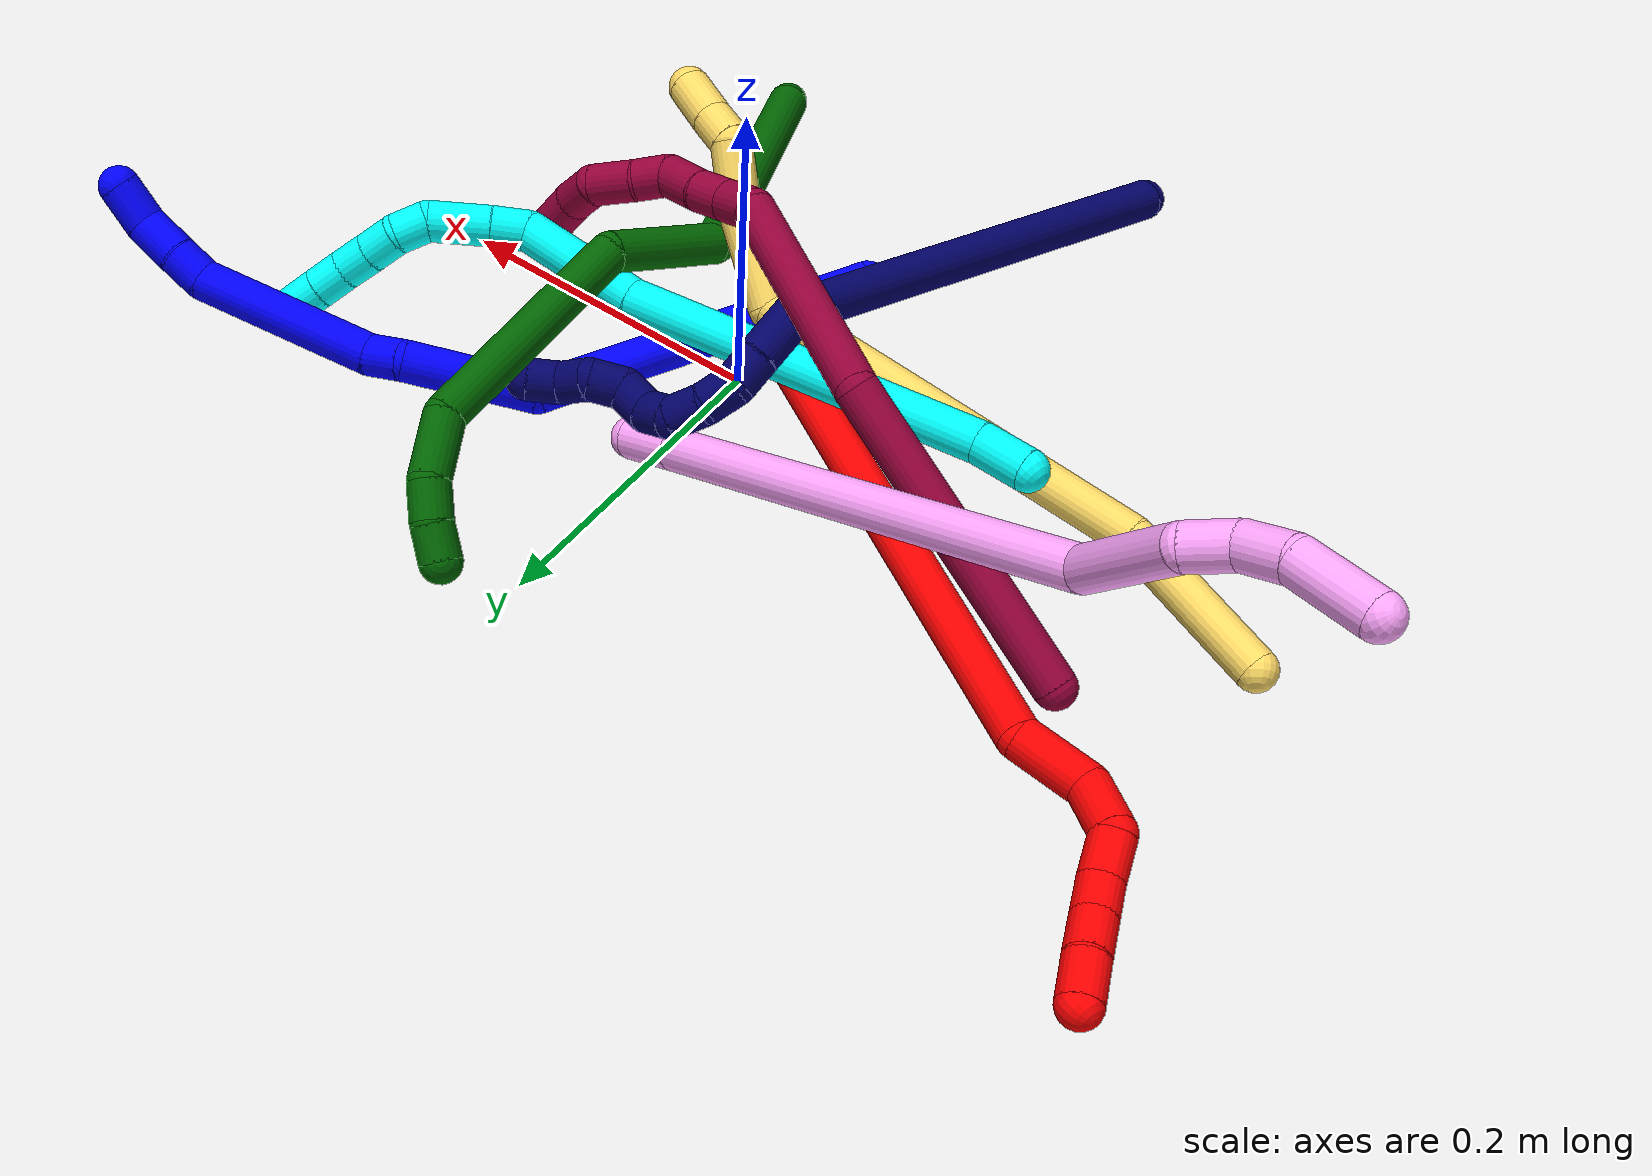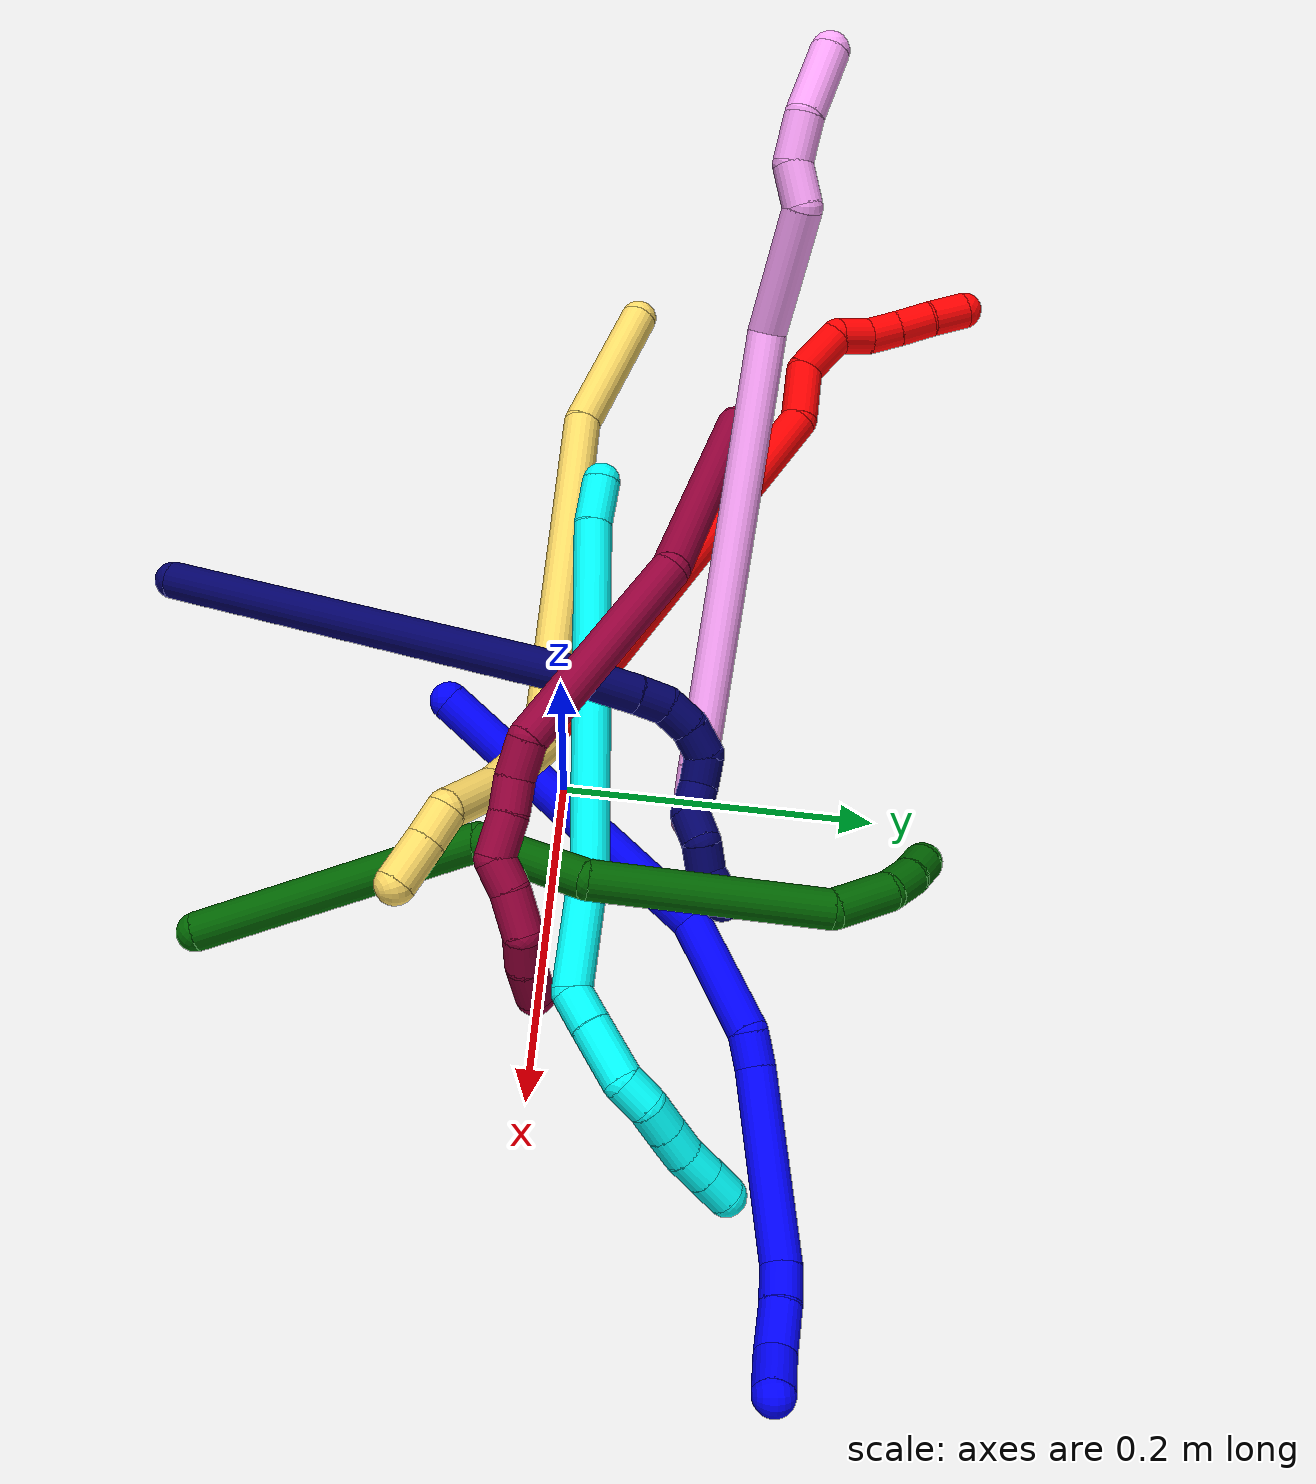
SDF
<sdf version="1.7">
 <world name="default">
  <plugin name="TubeGeneratorPlugin" filename="libtube_generator_plugin.so"/>
  <model name="photoneo_s_sensor">
   <static>1</static>
   <pose>0 0 2 1.57079 1.57079 3.14159</pose>
   <link name="link">
    <inertial><mass>0.1</mass></inertial>
    <sensor name="sensor" type="depth">
     <update_rate>30</update_rate>
     <camera>
      <horizontal_fov>1.22</horizontal_fov>
      <image><width>1920</width><height>1200</height><format>B8G8R8</format></image>
      <clip><near>0.1</near><far>4</far></clip>
      <depth_camera><output>points</output></depth_camera>
     </camera>
     <plugin name="camera_plugin" filename="libgazebo_ros_depth_camera.so">
      <baseline>0.2</baseline>
      <alwaysOn>1</alwaysOn>
      <updateRate>0.0</updateRate>
      <cameraName>camera_ir</cameraName>
      <imageTopicName>/camera/color/image_raw</imageTopicName>
      <cameraInfoTopicName>/camera/color/camera_info</cameraInfoTopicName>
      <depthImageTopicName>/camera/depth/image_raw</depthImageTopicName>
      <depthImageCameraInfoTopicName>/camera/depth/camera_info</depthImageCameraInfoTopicName>
      <pointCloudTopicName>/camera/depth/points</pointCloudTopicName>
      <frameName>fr_optical</frameName>
      <pointCloudCutoff>0.1</pointCloudCutoff>
      <pointCloudCutoffMax>2.0</pointCloudCutoffMax>
      <distortionK1>0</distortionK1>
      <distortionK2>0</distortionK2>
      <distortionK3>0</distortionK3>
      <distortionT1>0</distortionT1>
      <distortionT2>0</distortionT2>
      <CxPrime>0</CxPrime>
      <Cx>0</Cx>
      <Cy>0</Cy>
      <focalLength>0</focalLength>
      <hackBaseline>0</hackBaseline>
     </plugin>
    </sensor>
   </link>
  </model>
  <gravity>0 0 -9.8</gravity>
  <magnetic_field>6e-06 2.3e-05 -4.2e-05</magnetic_field>
  <atmosphere type="adiabatic"/>
  <physics name="default_physics" default="0" type="ode">
   <max_step_size>0.003</max_step_size>
   <real_time_factor>1</real_time_factor>
   <real_time_update_rate>1000</real_time_update_rate>
   <max_contacts>10000</max_contacts>
   <ode>
    <solver>
     <type>quick</type>
     <iters>100</iters>
     <sor>1.3</sor>
     <use_dynamic_moi_rescaling>0</use_dynamic_moi_rescaling>
    </solver>
    <constraints>
     <contact_max_correcting_vel>0</contact_max_correcting_vel>
     <contact_surface_layer>0.001</contact_surface_layer>
     <cfm>0</cfm>
     <erp>0.2</erp>
    </constraints>
   </ode>
  </physics>
  <scene><ambient>0.4 0.4 0.4 1</ambient><background>0.7 0.7 0.7 1</background><shadows>0</shadows></scene>
  <audio><device>default</device></audio>
  <spherical_coordinates>
   <surface_model>EARTH_WGS84</surface_model>
   <latitude_deg>0</latitude_deg>
   <longitude_deg>0</longitude_deg>
   <elevation>0</elevation>
   <heading_deg>0</heading_deg>
  </spherical_coordinates>
  <model name="bin">
   <static>1</static>
   <link name="bottom">
    <collision name="collision-bottom">
     <pose>0 0 -0.01 0 -0 0</pose>
     <geometry><box><size>0.8 0.6 0.02</size></box></geometry>
     <surface>
      <friction><ode><mu>100</mu><mu2>100</mu2></ode></friction>
      <contact><collide_bitmask>65535</collide_bitmask></contact>
     </surface>
    </collision>
   </link>
   <link name="west_wall">
    <collision name="collision-west_wall">
     <pose>-0.41 0 0.1 0 -0 0</pose>
     <geometry><box><size>0.02 0.6 0.2</size></box></geometry>
     <surface>
      <friction><ode><mu>100</mu><mu2>100</mu2></ode></friction>
      <contact><collide_bitmask>65535</collide_bitmask></contact>
     </surface>
    </collision>
   </link>
   <link name="east_wall">
    <collision name="collision-east_wall">
     <pose>0.41 0 0.1 0 -0 0</pose>
     <geometry><box><size>0.02 0.6 0.2</size></box></geometry>
     <surface>
      <friction><ode><mu>100</mu><mu2>100</mu2></ode></friction>
      <contact><collide_bitmask>65535</collide_bitmask></contact>
     </surface>
    </collision>
   </link>
   <link name="south_wall">
    <collision name="collision-south_wall">
     <pose>0 -0.31 0.1 0 -0 0</pose>
     <geometry><box><size>0.8 0.02 0.2</size></box></geometry>
     <surface>
      <friction><ode><mu>100</mu><mu2>100</mu2></ode></friction>
      <contact><collide_bitmask>65535</collide_bitmask></contact>
     </surface>
    </collision>
   </link>
   <link name="north_wall">
    <collision name="collision-north_wall">
     <pose>0 0.31 0.1 0 -0 0</pose>
     <geometry><box><size>0.8 0.02 0.2</size></box></geometry>
     <surface>
      <friction><ode><mu>100</mu><mu2>100</mu2></ode></friction>
      <contact><collide_bitmask>65535</collide_bitmask></contact>
     </surface>
    </collision>
   </link>
  </model>
  <model name="1">
   <static>0</static>
   <link name="1">
    <collision name="collision-cylinder-e_1_1_4">
     <pose>0.038962 0.059178 0.074381 -0.672057 0.389018 -0.137397</pose>
     <geometry><cylinder><radius>0.0125</radius><length>0.205451</length></cylinder></geometry>
     <surface>
      <friction><ode><mu>1.16</mu><mu2>1.16</mu2><slip1>0</slip1><slip2>0</slip2></ode></friction>
      <contact><ode><kp>1e+06</kp><kd>1</kd><max_vel>0</max_vel><min_depth>0.001</min_depth></ode></contact>
     </surface>
    </collision>
    <visual name="visual-cylinder-e_1_1_4">
     <pose>0.038962 0.059178 0.074381 -0.672057 0.389018 -0.137397</pose>
     <geometry><cylinder><radius>0.0125</radius><length>0.205451</length></cylinder></geometry>
     <material><ambient>0 0 1 1</ambient></material>
    </visual>
    <collision name="collision-cylinder-e_2_4_5">
     <pose>0.109553 0.138882 0.162872 -0.968546 0.903713 -0.499956</pose>
     <geometry><cylinder><radius>0.0125</radius><length>0.080519</length></cylinder></geometry>
     <surface>
      <friction><ode><mu>1.16</mu><mu2>1.16</mu2><slip1>0</slip1><slip2>0</slip2></ode></friction>
      <contact><ode><kp>1e+06</kp><kd>1</kd><max_vel>0</max_vel><min_depth>0.001</min_depth></ode></contact>
     </surface>
    </collision>
    <visual name="visual-cylinder-e_2_4_5">
     <pose>0.109553 0.138882 0.162872 -0.968546 0.903713 -0.499956</pose>
     <geometry><cylinder><radius>0.0125</radius><length>0.080519</length></cylinder></geometry>
     <material><ambient>0 0 1 1</ambient></material>
    </visual>
    <collision name="collision-cylinder-e_3_5_6">
     <pose>0.147479 0.168151 0.178678 -1.3793 0.615481 -0.512738</pose>
     <geometry><cylinder><radius>0.0125</radius><length>0.021815</length></cylinder></geometry>
     <surface>
      <friction><ode><mu>1.16</mu><mu2>1.16</mu2><slip1>0</slip1><slip2>0</slip2></ode></friction>
      <contact><ode><kp>1e+06</kp><kd>1</kd><max_vel>0</max_vel><min_depth>0.001</min_depth></ode></contact>
     </surface>
    </collision>
    <visual name="visual-cylinder-e_3_5_6">
     <pose>0.147479 0.168151 0.178678 -1.3793 0.615481 -0.512738</pose>
     <geometry><cylinder><radius>0.0125</radius><length>0.021815</length></cylinder></geometry>
     <material><ambient>0 0 1 1</ambient></material>
    </visual>
    <collision name="collision-cylinder-e_4_6_7">
     <pose>0.197058 0.214206 0.182724 -1.50786 0.858362 -0.811685</pose>
     <geometry><cylinder><radius>0.0125</radius><length>0.114384</length></cylinder></geometry>
     <surface>
      <friction><ode><mu>1.16</mu><mu2>1.16</mu2><slip1>0</slip1><slip2>0</slip2></ode></friction>
      <contact><ode><kp>1e+06</kp><kd>1</kd><max_vel>0</max_vel><min_depth>0.001</min_depth></ode></contact>
     </surface>
    </collision>
    <visual name="visual-cylinder-e_4_6_7">
     <pose>0.197058 0.214206 0.182724 -1.50786 0.858362 -0.811685</pose>
     <geometry><cylinder><radius>0.0125</radius><length>0.114384</length></cylinder></geometry>
     <material><ambient>0 0 1 1</ambient></material>
    </visual>
    <collision name="collision-cylinder-e_5_7_8">
     <pose>0.250347 0.256003 0.183392 -1.92976 1.12424 -1.47569</pose>
     <geometry><cylinder><radius>0.0125</radius><length>0.022191</length></cylinder></geometry>
     <surface>
      <friction><ode><mu>1.16</mu><mu2>1.16</mu2><slip1>0</slip1><slip2>0</slip2></ode></friction>
      <contact><ode><kp>1e+06</kp><kd>1</kd><max_vel>0</max_vel><min_depth>0.001</min_depth></ode></contact>
     </surface>
    </collision>
    <visual name="visual-cylinder-e_5_7_8">
     <pose>0.250347 0.256003 0.183392 -1.92976 1.12424 -1.47569</pose>
     <geometry><cylinder><radius>0.0125</radius><length>0.022191</length></cylinder></geometry>
     <material><ambient>0 0 1 1</ambient></material>
    </visual>
    <collision name="collision-cylinder-e_6_8_9">
     <pose>0.272377 0.267362 0.178492 -2.00856 1.00777 -1.42837</pose>
     <geometry><cylinder><radius>0.0125</radius><length>0.028435</length></cylinder></geometry>
     <surface>
      <friction><ode><mu>1.16</mu><mu2>1.16</mu2><slip1>0</slip1><slip2>0</slip2></ode></friction>
      <contact><ode><kp>1e+06</kp><kd>1</kd><max_vel>0</max_vel><min_depth>0.001</min_depth></ode></contact>
     </surface>
    </collision>
    <visual name="visual-cylinder-e_6_8_9">
     <pose>0.272377 0.267362 0.178492 -2.00856 1.00777 -1.42837</pose>
     <geometry><cylinder><radius>0.0125</radius><length>0.028435</length></cylinder></geometry>
     <material><ambient>0 0 1 1</ambient></material>
    </visual>
    <collision name="collision-cylinder-e_7_9_2">
     <pose>0.297696 0.275284 0.172603 -2.7674 1.35818 -2.68084</pose>
     <geometry><cylinder><radius>0.0125</radius><length>0.027205</length></cylinder></geometry>
     <surface>
      <friction><ode><mu>1.16</mu><mu2>1.16</mu2><slip1>0</slip1><slip2>0</slip2></ode></friction>
      <contact><ode><kp>1e+06</kp><kd>1</kd><max_vel>0</max_vel><min_depth>0.001</min_depth></ode></contact>
     </surface>
    </collision>
    <visual name="visual-cylinder-e_7_9_2">
     <pose>0.297696 0.275284 0.172603 -2.7674 1.35818 -2.68084</pose>
     <geometry><cylinder><radius>0.0125</radius><length>0.027205</length></cylinder></geometry>
     <material><ambient>0 0 1 1</ambient></material>
    </visual>
    <collision name="collision-sphere-2">
     <pose>0.310992 0.276334 0.169932 0 -0 0</pose>
     <geometry><sphere><radius>0.0125</radius></sphere></geometry>
     <surface>
      <friction><ode><mu>1.16</mu><mu2>1.16</mu2><slip1>0</slip1><slip2>0</slip2></ode></friction>
      <contact><ode><kp>1e+06</kp><kd>1</kd><max_vel>0</max_vel><min_depth>0.001</min_depth></ode></contact>
     </surface>
    </collision>
    <visual name="visual-sphere-2">
     <pose>0.310992 0.276334 0.169932 0 -0 0</pose>
     <geometry><sphere><radius>0.0125</radius></sphere></geometry>
     <material><ambient>0 0 1 1</ambient></material>
    </visual>
    <collision name="collision-sphere-9">
     <pose>0.2844 0.274235 0.175275 0 -0 0</pose>
     <geometry><sphere><radius>0.0125</radius></sphere></geometry>
     <surface>
      <friction><ode><mu>1.16</mu><mu2>1.16</mu2><slip1>0</slip1><slip2>0</slip2></ode></friction>
      <contact><ode><kp>1e+06</kp><kd>1</kd><max_vel>0</max_vel><min_depth>0.001</min_depth></ode></contact>
     </surface>
    </collision>
    <visual name="visual-sphere-9">
     <pose>0.2844 0.274235 0.175275 0 -0 0</pose>
     <geometry><sphere><radius>0.0125</radius></sphere></geometry>
     <material><ambient>0 0 1 1</ambient></material>
    </visual>
    <collision name="collision-sphere-4">
     <pose>0.077923 0.118356 0.148761 0 -0 0</pose>
     <geometry><sphere><radius>0.0125</radius></sphere></geometry>
     <surface>
      <friction><ode><mu>1.16</mu><mu2>1.16</mu2><slip1>0</slip1><slip2>0</slip2></ode></friction>
      <contact><ode><kp>1e+06</kp><kd>1</kd><max_vel>0</max_vel><min_depth>0.001</min_depth></ode></contact>
     </surface>
    </collision>
    <visual name="visual-sphere-4">
     <pose>0.077923 0.118356 0.148761 0 -0 0</pose>
     <geometry><sphere><radius>0.0125</radius></sphere></geometry>
     <material><ambient>0 0 1 1</ambient></material>
    </visual>
    <collision name="collision-sphere-1">
     <geometry><sphere><radius>0.0125</radius></sphere></geometry>
     <surface>
      <friction><ode><mu>1.16</mu><mu2>1.16</mu2><slip1>0</slip1><slip2>0</slip2></ode></friction>
      <contact><ode><kp>1e+06</kp><kd>1</kd><max_vel>0</max_vel><min_depth>0.001</min_depth></ode></contact>
     </surface>
    </collision>
    <visual name="visual-sphere-1">
     <geometry><sphere><radius>0.0125</radius></sphere></geometry>
     <material><ambient>0 0 1 1</ambient></material>
    </visual>
    <collision name="collision-sphere-8">
     <pose>0.260355 0.260489 0.181709 0 -0 0</pose>
     <geometry><sphere><radius>0.0125</radius></sphere></geometry>
     <surface>
      <friction><ode><mu>1.16</mu><mu2>1.16</mu2><slip1>0</slip1><slip2>0</slip2></ode></friction>
      <contact><ode><kp>1e+06</kp><kd>1</kd><max_vel>0</max_vel><min_depth>0.001</min_depth></ode></contact>
     </surface>
    </collision>
    <visual name="visual-sphere-8">
     <pose>0.260355 0.260489 0.181709 0 -0 0</pose>
     <geometry><sphere><radius>0.0125</radius></sphere></geometry>
     <material><ambient>0 0 1 1</ambient></material>
    </visual>
    <collision name="collision-sphere-5">
     <pose>0.141182 0.159408 0.176983 0 -0 0</pose>
     <geometry><sphere><radius>0.0125</radius></sphere></geometry>
     <surface>
      <friction><ode><mu>1.16</mu><mu2>1.16</mu2><slip1>0</slip1><slip2>0</slip2></ode></friction>
      <contact><ode><kp>1e+06</kp><kd>1</kd><max_vel>0</max_vel><min_depth>0.001</min_depth></ode></contact>
     </surface>
    </collision>
    <visual name="visual-sphere-5">
     <pose>0.141182 0.159408 0.176983 0 -0 0</pose>
     <geometry><sphere><radius>0.0125</radius></sphere></geometry>
     <material><ambient>0 0 1 1</ambient></material>
    </visual>
    <collision name="collision-sphere-6">
     <pose>0.153777 0.176895 0.180373 0 -0 0</pose>
     <geometry><sphere><radius>0.0125</radius></sphere></geometry>
     <surface>
      <friction><ode><mu>1.16</mu><mu2>1.16</mu2><slip1>0</slip1><slip2>0</slip2></ode></friction>
      <contact><ode><kp>1e+06</kp><kd>1</kd><max_vel>0</max_vel><min_depth>0.001</min_depth></ode></contact>
     </surface>
    </collision>
    <visual name="visual-sphere-6">
     <pose>0.153777 0.176895 0.180373 0 -0 0</pose>
     <geometry><sphere><radius>0.0125</radius></sphere></geometry>
     <material><ambient>0 0 1 1</ambient></material>
    </visual>
    <collision name="collision-sphere-7">
     <pose>0.240339 0.251517 0.185076 0 -0 0</pose>
     <geometry><sphere><radius>0.0125</radius></sphere></geometry>
     <surface>
      <friction><ode><mu>1.16</mu><mu2>1.16</mu2><slip1>0</slip1><slip2>0</slip2></ode></friction>
      <contact><ode><kp>1e+06</kp><kd>1</kd><max_vel>0</max_vel><min_depth>0.001</min_depth></ode></contact>
     </surface>
    </collision>
    <visual name="visual-sphere-7">
     <pose>0.240339 0.251517 0.185076 0 -0 0</pose>
     <geometry><sphere><radius>0.0125</radius></sphere></geometry>
     <material><ambient>0 0 1 1</ambient></material>
    </visual>
    <inertial>
     <pose>0.127965 0.144566 0.13407 0 -0 0</pose>
     <mass>0.5</mass>
     <inertia>
      <ixx>0.000607</ixx>
      <ixy>0</ixy>
      <ixz>0</ixz>
      <iyy>0.000562</iyy>
      <iyz>0</iyz>
      <izz>-0.000939</izz>
     </inertia>
    </inertial>
   </link>
   <pose>-0.0364 -0.077038 0.04496 -1.66129 -0.817332 0.21813</pose>
  </model>
  <model name="2">
   <static>0</static>
   <link name="2">
    <collision name="collision-cylinder-e_1_1_4">
     <pose>-0.022821 0.021688 0.159924 -0.134793 -0.140474 0.009497</pose>
     <geometry><cylinder><radius>0.0125</radius><length>0.325986</length></cylinder></geometry>
     <surface>
      <friction><ode><mu>1.16</mu><mu2>1.16</mu2><slip1>0</slip1><slip2>0</slip2></ode></friction>
      <contact><ode><kp>1e+06</kp><kd>1</kd><max_vel>0</max_vel><min_depth>0.001</min_depth></ode></contact>
     </surface>
    </collision>
    <visual name="visual-cylinder-e_1_1_4">
     <pose>-0.022821 0.021688 0.159924 -0.134793 -0.140474 0.009497</pose>
     <geometry><cylinder><radius>0.0125</radius><length>0.325986</length></cylinder></geometry>
     <material><ambient>1 0 0 1</ambient></material>
    </visual>
    <collision name="collision-cylinder-e_2_4_5">
     <pose>-0.042325 0.037241 0.340003 0.295457 0.156167 0.023286</pose>
     <geometry><cylinder><radius>0.0125</radius><length>0.042657</length></cylinder></geometry>
     <surface>
      <friction><ode><mu>1.16</mu><mu2>1.16</mu2><slip1>0</slip1><slip2>0</slip2></ode></friction>
      <contact><ode><kp>1e+06</kp><kd>1</kd><max_vel>0</max_vel><min_depth>0.001</min_depth></ode></contact>
     </surface>
    </collision>
    <visual name="visual-cylinder-e_2_4_5">
     <pose>-0.042325 0.037241 0.340003 0.295457 0.156167 0.023286</pose>
     <geometry><cylinder><radius>0.0125</radius><length>0.042657</length></cylinder></geometry>
     <material><ambient>1 0 0 1</ambient></material>
    </visual>
    <collision name="collision-cylinder-e_3_5_6">
     <pose>-0.041144 0.0367 0.376159 -0.336333 -0.125382 0.021313</pose>
     <geometry><cylinder><radius>0.0125</radius><length>0.034168</length></cylinder></geometry>
     <surface>
      <friction><ode><mu>1.16</mu><mu2>1.16</mu2><slip1>0</slip1><slip2>0</slip2></ode></friction>
      <contact><ode><kp>1e+06</kp><kd>1</kd><max_vel>0</max_vel><min_depth>0.001</min_depth></ode></contact>
     </surface>
    </collision>
    <visual name="visual-cylinder-e_3_5_6">
     <pose>-0.041144 0.0367 0.376159 -0.336333 -0.125382 0.021313</pose>
     <geometry><cylinder><radius>0.0125</radius><length>0.034168</length></cylinder></geometry>
     <material><ambient>1 0 0 1</ambient></material>
    </visual>
    <collision name="collision-cylinder-e_4_6_7">
     <pose>-0.053106 0.045101 0.399405 -0.369561 -0.901663 0.18047</pose>
     <geometry><cylinder><radius>0.0125</radius><length>0.025054</length></cylinder></geometry>
     <surface>
      <friction><ode><mu>1.16</mu><mu2>1.16</mu2><slip1>0</slip1><slip2>0</slip2></ode></friction>
      <contact><ode><kp>1e+06</kp><kd>1</kd><max_vel>0</max_vel><min_depth>0.001</min_depth></ode></contact>
     </surface>
    </collision>
    <visual name="visual-cylinder-e_4_6_7">
     <pose>-0.053106 0.045101 0.399405 -0.369561 -0.901663 0.18047</pose>
     <geometry><cylinder><radius>0.0125</radius><length>0.025054</length></cylinder></geometry>
     <material><ambient>1 0 0 1</ambient></material>
    </visual>
    <collision name="collision-cylinder-e_5_7_8">
     <pose>-0.069153 0.053515 0.414184 -0.63983 -0.58514 0.198923</pose>
     <geometry><cylinder><radius>0.0125</radius><length>0.02253</length></cylinder></geometry>
     <surface>
      <friction><ode><mu>1.16</mu><mu2>1.16</mu2><slip1>0</slip1><slip2>0</slip2></ode></friction>
      <contact><ode><kp>1e+06</kp><kd>1</kd><max_vel>0</max_vel><min_depth>0.001</min_depth></ode></contact>
     </surface>
    </collision>
    <visual name="visual-cylinder-e_5_7_8">
     <pose>-0.069153 0.053515 0.414184 -0.63983 -0.58514 0.198923</pose>
     <geometry><cylinder><radius>0.0125</radius><length>0.02253</length></cylinder></geometry>
     <material><ambient>1 0 0 1</ambient></material>
    </visual>
    <collision name="collision-cylinder-e_6_8_9">
     <pose>-0.081408 0.065794 0.429798 -0.690268 -0.522332 0.191592</pose>
     <geometry><cylinder><radius>0.0125</radius><length>0.024183</length></cylinder></geometry>
     <surface>
      <friction><ode><mu>1.16</mu><mu2>1.16</mu2><slip1>0</slip1><slip2>0</slip2></ode></friction>
      <contact><ode><kp>1e+06</kp><kd>1</kd><max_vel>0</max_vel><min_depth>0.001</min_depth></ode></contact>
     </surface>
    </collision>
    <visual name="visual-cylinder-e_6_8_9">
     <pose>-0.081408 0.065794 0.429798 -0.690268 -0.522332 0.191592</pose>
     <geometry><cylinder><radius>0.0125</radius><length>0.024183</length></cylinder></geometry>
     <material><ambient>1 0 0 1</ambient></material>
    </visual>
    <collision name="collision-cylinder-e_7_9_2">
     <pose>-0.094875 0.077933 0.44662 -0.558814 -0.624763 0.184792</pose>
     <geometry><cylinder><radius>0.0125</radius><length>0.025423</length></cylinder></geometry>
     <surface>
      <friction><ode><mu>1.16</mu><mu2>1.16</mu2><slip1>0</slip1><slip2>0</slip2></ode></friction>
      <contact><ode><kp>1e+06</kp><kd>1</kd><max_vel>0</max_vel><min_depth>0.001</min_depth></ode></contact>
     </surface>
    </collision>
    <visual name="visual-cylinder-e_7_9_2">
     <pose>-0.094875 0.077933 0.44662 -0.558814 -0.624763 0.184792</pose>
     <geometry><cylinder><radius>0.0125</radius><length>0.025423</length></cylinder></geometry>
     <material><ambient>1 0 0 1</ambient></material>
    </visual>
    <collision name="collision-sphere-2">
     <pose>-0.10231 0.083399 0.455362 0 -0 0</pose>
     <geometry><sphere><radius>0.0125</radius></sphere></geometry>
     <surface>
      <friction><ode><mu>1.16</mu><mu2>1.16</mu2><slip1>0</slip1><slip2>0</slip2></ode></friction>
      <contact><ode><kp>1e+06</kp><kd>1</kd><max_vel>0</max_vel><min_depth>0.001</min_depth></ode></contact>
     </surface>
    </collision>
    <visual name="visual-sphere-2">
     <pose>-0.10231 0.083399 0.455362 0 -0 0</pose>
     <geometry><sphere><radius>0.0125</radius></sphere></geometry>
     <material><ambient>1 0 0 1</ambient></material>
    </visual>
    <collision name="collision-sphere-9">
     <pose>-0.08744 0.072467 0.437878 0 -0 0</pose>
     <geometry><sphere><radius>0.0125</radius></sphere></geometry>
     <surface>
      <friction><ode><mu>1.16</mu><mu2>1.16</mu2><slip1>0</slip1><slip2>0</slip2></ode></friction>
      <contact><ode><kp>1e+06</kp><kd>1</kd><max_vel>0</max_vel><min_depth>0.001</min_depth></ode></contact>
     </surface>
    </collision>
    <visual name="visual-sphere-9">
     <pose>-0.08744 0.072467 0.437878 0 -0 0</pose>
     <geometry><sphere><radius>0.0125</radius></sphere></geometry>
     <material><ambient>1 0 0 1</ambient></material>
    </visual>
    <collision name="collision-sphere-4">
     <pose>-0.045642 0.043376 0.319847 0 -0 0</pose>
     <geometry><sphere><radius>0.0125</radius></sphere></geometry>
     <surface>
      <friction><ode><mu>1.16</mu><mu2>1.16</mu2><slip1>0</slip1><slip2>0</slip2></ode></friction>
      <contact><ode><kp>1e+06</kp><kd>1</kd><max_vel>0</max_vel><min_depth>0.001</min_depth></ode></contact>
     </surface>
    </collision>
    <visual name="visual-sphere-4">
     <pose>-0.045642 0.043376 0.319847 0 -0 0</pose>
     <geometry><sphere><radius>0.0125</radius></sphere></geometry>
     <material><ambient>1 0 0 1</ambient></material>
    </visual>
    <collision name="collision-sphere-1">
     <geometry><sphere><radius>0.0125</radius></sphere></geometry>
     <surface>
      <friction><ode><mu>1.16</mu><mu2>1.16</mu2><slip1>0</slip1><slip2>0</slip2></ode></friction>
      <contact><ode><kp>1e+06</kp><kd>1</kd><max_vel>0</max_vel><min_depth>0.001</min_depth></ode></contact>
     </surface>
    </collision>
    <visual name="visual-sphere-1">
     <geometry><sphere><radius>0.0125</radius></sphere></geometry>
     <material><ambient>1 0 0 1</ambient></material>
    </visual>
    <collision name="collision-sphere-8">
     <pose>-0.075375 0.059121 0.421718 0 -0 0</pose>
     <geometry><sphere><radius>0.0125</radius></sphere></geometry>
     <surface>
      <friction><ode><mu>1.16</mu><mu2>1.16</mu2><slip1>0</slip1><slip2>0</slip2></ode></friction>
      <contact><ode><kp>1e+06</kp><kd>1</kd><max_vel>0</max_vel><min_depth>0.001</min_depth></ode></contact>
     </surface>
    </collision>
    <visual name="visual-sphere-8">
     <pose>-0.075375 0.059121 0.421718 0 -0 0</pose>
     <geometry><sphere><radius>0.0125</radius></sphere></geometry>
     <material><ambient>1 0 0 1</ambient></material>
    </visual>
    <collision name="collision-sphere-5">
     <pose>-0.039008 0.031106 0.360159 0 -0 0</pose>
     <geometry><sphere><radius>0.0125</radius></sphere></geometry>
     <surface>
      <friction><ode><mu>1.16</mu><mu2>1.16</mu2><slip1>0</slip1><slip2>0</slip2></ode></friction>
      <contact><ode><kp>1e+06</kp><kd>1</kd><max_vel>0</max_vel><min_depth>0.001</min_depth></ode></contact>
     </surface>
    </collision>
    <visual name="visual-sphere-5">
     <pose>-0.039008 0.031106 0.360159 0 -0 0</pose>
     <geometry><sphere><radius>0.0125</radius></sphere></geometry>
     <material><ambient>1 0 0 1</ambient></material>
    </visual>
    <collision name="collision-sphere-6">
     <pose>-0.04328 0.042294 0.392159 0 -0 0</pose>
     <geometry><sphere><radius>0.0125</radius></sphere></geometry>
     <surface>
      <friction><ode><mu>1.16</mu><mu2>1.16</mu2><slip1>0</slip1><slip2>0</slip2></ode></friction>
      <contact><ode><kp>1e+06</kp><kd>1</kd><max_vel>0</max_vel><min_depth>0.001</min_depth></ode></contact>
     </surface>
    </collision>
    <visual name="visual-sphere-6">
     <pose>-0.04328 0.042294 0.392159 0 -0 0</pose>
     <geometry><sphere><radius>0.0125</radius></sphere></geometry>
     <material><ambient>1 0 0 1</ambient></material>
    </visual>
    <collision name="collision-sphere-7">
     <pose>-0.062932 0.047908 0.406651 0 -0 0</pose>
     <geometry><sphere><radius>0.0125</radius></sphere></geometry>
     <surface>
      <friction><ode><mu>1.16</mu><mu2>1.16</mu2><slip1>0</slip1><slip2>0</slip2></ode></friction>
      <contact><ode><kp>1e+06</kp><kd>1</kd><max_vel>0</max_vel><min_depth>0.001</min_depth></ode></contact>
     </surface>
    </collision>
    <visual name="visual-sphere-7">
     <pose>-0.062932 0.047908 0.406651 0 -0 0</pose>
     <geometry><sphere><radius>0.0125</radius></sphere></geometry>
     <material><ambient>1 0 0 1</ambient></material>
    </visual>
    <inertial>
     <pose>-0.035839 0.031641 0.24115 0 -0 0</pose>
     <mass>0.5</mass>
     <inertia>
      <ixx>0.002911</ixx>
      <ixy>0</ixy>
      <ixz>0</ixz>
      <iyy>0.002929</iyy>
      <iyz>0</iyz>
      <izz>5.7e-05</izz>
     </inertia>
    </inertial>
   </link>
   <pose>0.002777 -0.035945 0.011422 1.54952 -0.720383 -1.90018</pose>
  </model>
  <model name="3">
   <static>0</static>
   <link name="3">
    <collision name="collision-cylinder-e_1_1_4">
     <pose>0.003811 -0.001877 0.015196 0.122875 0.243915 0.015079</pose>
     <geometry><cylinder><radius>0.0125</radius><length>0.031558</length></cylinder></geometry>
     <surface>
      <friction><ode><mu>1.16</mu><mu2>1.16</mu2><slip1>0</slip1><slip2>0</slip2></ode></friction>
      <contact><ode><kp>1e+06</kp><kd>1</kd><max_vel>0</max_vel><min_depth>0.001</min_depth></ode></contact>
     </surface>
    </collision>
    <visual name="visual-cylinder-e_1_1_4">
     <pose>0.003811 -0.001877 0.015196 0.122875 0.243915 0.015079</pose>
     <geometry><cylinder><radius>0.0125</radius><length>0.031558</length></cylinder></geometry>
     <material><ambient>0.003922 1 0.996078 1</ambient></material>
    </visual>
    <collision name="collision-cylinder-e_2_4_5">
     <pose>0.051763 -0.010143 0.134439 0.061339 0.400562 0.012456</pose>
     <geometry><cylinder><radius>0.0125</radius><length>0.226406</length></cylinder></geometry>
     <surface>
      <friction><ode><mu>1.16</mu><mu2>1.16</mu2><slip1>0</slip1><slip2>0</slip2></ode></friction>
      <contact><ode><kp>1e+06</kp><kd>1</kd><max_vel>0</max_vel><min_depth>0.001</min_depth></ode></contact>
     </surface>
    </collision>
    <visual name="visual-cylinder-e_2_4_5">
     <pose>0.051763 -0.010143 0.134439 0.061339 0.400562 0.012456</pose>
     <geometry><cylinder><radius>0.0125</radius><length>0.226406</length></cylinder></geometry>
     <material><ambient>0.003922 1 0.996078 1</ambient></material>
    </visual>
    <collision name="collision-cylinder-e_3_5_6">
     <pose>0.105539 -0.016355 0.277706 -0.004558 0.240845 -0.000552</pose>
     <geometry><cylinder><radius>0.0125</radius><length>0.080776</length></cylinder></geometry>
     <surface>
      <friction><ode><mu>1.16</mu><mu2>1.16</mu2><slip1>0</slip1><slip2>0</slip2></ode></friction>
      <contact><ode><kp>1e+06</kp><kd>1</kd><max_vel>0</max_vel><min_depth>0.001</min_depth></ode></contact>
     </surface>
    </collision>
    <visual name="visual-cylinder-e_3_5_6">
     <pose>0.105539 -0.016355 0.277706 -0.004558 0.240845 -0.000552</pose>
     <geometry><cylinder><radius>0.0125</radius><length>0.080776</length></cylinder></geometry>
     <material><ambient>0.003922 1 0.996078 1</ambient></material>
    </visual>
    <collision name="collision-cylinder-e_4_6_7">
     <pose>0.123274 -0.012983 0.324436 -0.402129 0.78196 -0.167634</pose>
     <geometry><cylinder><radius>0.0125</radius><length>0.022996</length></cylinder></geometry>
     <surface>
      <friction><ode><mu>1.16</mu><mu2>1.16</mu2><slip1>0</slip1><slip2>0</slip2></ode></friction>
      <contact><ode><kp>1e+06</kp><kd>1</kd><max_vel>0</max_vel><min_depth>0.001</min_depth></ode></contact>
     </surface>
    </collision>
    <visual name="visual-cylinder-e_4_6_7">
     <pose>0.123274 -0.012983 0.324436 -0.402129 0.78196 -0.167634</pose>
     <geometry><cylinder><radius>0.0125</radius><length>0.022996</length></cylinder></geometry>
     <material><ambient>0.003922 1 0.996078 1</ambient></material>
    </visual>
    <collision name="collision-cylinder-e_5_7_8">
     <pose>0.145055 -0.005389 0.343819 -0.354893 0.823859 -0.156391</pose>
     <geometry><cylinder><radius>0.0125</radius><length>0.037283</length></cylinder></geometry>
     <surface>
      <friction><ode><mu>1.16</mu><mu2>1.16</mu2><slip1>0</slip1><slip2>0</slip2></ode></friction>
      <contact><ode><kp>1e+06</kp><kd>1</kd><max_vel>0</max_vel><min_depth>0.001</min_depth></ode></contact>
     </surface>
    </collision>
    <visual name="visual-cylinder-e_5_7_8">
     <pose>0.145055 -0.005389 0.343819 -0.354893 0.823859 -0.156391</pose>
     <geometry><cylinder><radius>0.0125</radius><length>0.037283</length></cylinder></geometry>
     <material><ambient>0.003922 1 0.996078 1</ambient></material>
    </visual>
    <collision name="collision-cylinder-e_6_8_9">
     <pose>0.168475 -0.001189 0.358829 0.063952 1.25887 0.046581</pose>
     <geometry><cylinder><radius>0.0125</radius><length>0.020469</length></cylinder></geometry>
     <surface>
      <friction><ode><mu>1.16</mu><mu2>1.16</mu2><slip1>0</slip1><slip2>0</slip2></ode></friction>
      <contact><ode><kp>1e+06</kp><kd>1</kd><max_vel>0</max_vel><min_depth>0.001</min_depth></ode></contact>
     </surface>
    </collision>
    <visual name="visual-cylinder-e_6_8_9">
     <pose>0.168475 -0.001189 0.358829 0.063952 1.25887 0.046581</pose>
     <geometry><cylinder><radius>0.0125</radius><length>0.020469</length></cylinder></geometry>
     <material><ambient>0.003922 1 0.996078 1</ambient></material>
    </visual>
    <collision name="collision-cylinder-e_7_9_10">
     <pose>0.187173 -0.005111 0.364743 0.929272 1.09238 0.591508</pose>
     <geometry><cylinder><radius>0.0125</radius><length>0.02018</length></cylinder></geometry>
     <surface>
      <friction><ode><mu>1.16</mu><mu2>1.16</mu2><slip1>0</slip1><slip2>0</slip2></ode></friction>
      <contact><ode><kp>1e+06</kp><kd>1</kd><max_vel>0</max_vel><min_depth>0.001</min_depth></ode></contact>
     </surface>
    </collision>
    <visual name="visual-cylinder-e_7_9_10">
     <pose>0.187173 -0.005111 0.364743 0.929272 1.09238 0.591508</pose>
     <geometry><cylinder><radius>0.0125</radius><length>0.02018</length></cylinder></geometry>
     <material><ambient>0.003922 1 0.996078 1</ambient></material>
    </visual>
    <collision name="collision-cylinder-e_8_10_11">
     <pose>0.205139 -0.012241 0.370285 0.889867 1.11765 0.579541</pose>
     <geometry><cylinder><radius>0.0125</radius><length>0.020041</length></cylinder></geometry>
     <surface>
      <friction><ode><mu>1.16</mu><mu2>1.16</mu2><slip1>0</slip1><slip2>0</slip2></ode></friction>
      <contact><ode><kp>1e+06</kp><kd>1</kd><max_vel>0</max_vel><min_depth>0.001</min_depth></ode></contact>
     </surface>
    </collision>
    <visual name="visual-cylinder-e_8_10_11">
     <pose>0.205139 -0.012241 0.370285 0.889867 1.11765 0.579541</pose>
     <geometry><cylinder><radius>0.0125</radius><length>0.020041</length></cylinder></geometry>
     <material><ambient>0.003922 1 0.996078 1</ambient></material>
    </visual>
    <collision name="collision-cylinder-e_9_11_12">
     <pose>0.223673 -0.0181 0.374958 0.908211 1.25546 0.68084</pose>
     <geometry><cylinder><radius>0.0125</radius><length>0.020039</length></cylinder></geometry>
     <surface>
      <friction><ode><mu>1.16</mu><mu2>1.16</mu2><slip1>0</slip1><slip2>0</slip2></ode></friction>
      <contact><ode><kp>1e+06</kp><kd>1</kd><max_vel>0</max_vel><min_depth>0.001</min_depth></ode></contact>
     </surface>
    </collision>
    <visual name="visual-cylinder-e_9_11_12">
     <pose>0.223673 -0.0181 0.374958 0.908211 1.25546 0.68084</pose>
     <geometry><cylinder><radius>0.0125</radius><length>0.020039</length></cylinder></geometry>
     <material><ambient>0.003922 1 0.996078 1</ambient></material>
    </visual>
    <collision name="collision-cylinder-e_10_12_2">
     <pose>0.242826 -0.023056 0.378763 0.923787 1.25539 0.693242</pose>
     <geometry><cylinder><radius>0.0125</radius><length>0.020253</length></cylinder></geometry>
     <surface>
      <friction><ode><mu>1.16</mu><mu2>1.16</mu2><slip1>0</slip1><slip2>0</slip2></ode></friction>
      <contact><ode><kp>1e+06</kp><kd>1</kd><max_vel>0</max_vel><min_depth>0.001</min_depth></ode></contact>
     </surface>
    </collision>
    <visual name="visual-cylinder-e_10_12_2">
     <pose>0.242826 -0.023056 0.378763 0.923787 1.25539 0.693242</pose>
     <geometry><cylinder><radius>0.0125</radius><length>0.020253</length></cylinder></geometry>
     <material><ambient>0.003922 1 0.996078 1</ambient></material>
    </visual>
    <collision name="collision-sphere-2">
     <pose>0.252452 -0.025562 0.380656 0 -0 0</pose>
     <geometry><sphere><radius>0.0125</radius></sphere></geometry>
     <surface>
      <friction><ode><mu>1.16</mu><mu2>1.16</mu2><slip1>0</slip1><slip2>0</slip2></ode></friction>
      <contact><ode><kp>1e+06</kp><kd>1</kd><max_vel>0</max_vel><min_depth>0.001</min_depth></ode></contact>
     </surface>
    </collision>
    <visual name="visual-sphere-2">
     <pose>0.252452 -0.025562 0.380656 0 -0 0</pose>
     <geometry><sphere><radius>0.0125</radius></sphere></geometry>
     <material><ambient>0.003922 1 0.996078 1</ambient></material>
    </visual>
    <collision name="collision-sphere-12">
     <pose>0.233199 -0.02055 0.376869 0 -0 0</pose>
     <geometry><sphere><radius>0.0125</radius></sphere></geometry>
     <surface>
      <friction><ode><mu>1.16</mu><mu2>1.16</mu2><slip1>0</slip1><slip2>0</slip2></ode></friction>
      <contact><ode><kp>1e+06</kp><kd>1</kd><max_vel>0</max_vel><min_depth>0.001</min_depth></ode></contact>
     </surface>
    </collision>
    <visual name="visual-sphere-12">
     <pose>0.233199 -0.02055 0.376869 0 -0 0</pose>
     <geometry><sphere><radius>0.0125</radius></sphere></geometry>
     <material><ambient>0.003922 1 0.996078 1</ambient></material>
    </visual>
    <collision name="collision-sphere-11">
     <pose>0.214148 -0.01565 0.373046 0 -0 0</pose>
     <geometry><sphere><radius>0.0125</radius></sphere></geometry>
     <surface>
      <friction><ode><mu>1.16</mu><mu2>1.16</mu2><slip1>0</slip1><slip2>0</slip2></ode></friction>
      <contact><ode><kp>1e+06</kp><kd>1</kd><max_vel>0</max_vel><min_depth>0.001</min_depth></ode></contact>
     </surface>
    </collision>
    <visual name="visual-sphere-11">
     <pose>0.214148 -0.01565 0.373046 0 -0 0</pose>
     <geometry><sphere><radius>0.0125</radius></sphere></geometry>
     <material><ambient>0.003922 1 0.996078 1</ambient></material>
    </visual>
    <collision name="collision-sphere-10">
     <pose>0.19613 -0.008833 0.367523 0 -0 0</pose>
     <geometry><sphere><radius>0.0125</radius></sphere></geometry>
     <surface>
      <friction><ode><mu>1.16</mu><mu2>1.16</mu2><slip1>0</slip1><slip2>0</slip2></ode></friction>
      <contact><ode><kp>1e+06</kp><kd>1</kd><max_vel>0</max_vel><min_depth>0.001</min_depth></ode></contact>
     </surface>
    </collision>
    <visual name="visual-sphere-10">
     <pose>0.19613 -0.008833 0.367523 0 -0 0</pose>
     <geometry><sphere><radius>0.0125</radius></sphere></geometry>
     <material><ambient>0.003922 1 0.996078 1</ambient></material>
    </visual>
    <collision name="collision-sphere-9">
     <pose>0.178216 -0.00139 0.361964 0 -0 0</pose>
     <geometry><sphere><radius>0.0125</radius></sphere></geometry>
     <surface>
      <friction><ode><mu>1.16</mu><mu2>1.16</mu2><slip1>0</slip1><slip2>0</slip2></ode></friction>
      <contact><ode><kp>1e+06</kp><kd>1</kd><max_vel>0</max_vel><min_depth>0.001</min_depth></ode></contact>
     </surface>
    </collision>
    <visual name="visual-sphere-9">
     <pose>0.178216 -0.00139 0.361964 0 -0 0</pose>
     <geometry><sphere><radius>0.0125</radius></sphere></geometry>
     <material><ambient>0.003922 1 0.996078 1</ambient></material>
    </visual>
    <collision name="collision-sphere-4">
     <pose>0.007621 -0.003753 0.030393 0 -0 0</pose>
     <geometry><sphere><radius>0.0125</radius></sphere></geometry>
     <surface>
      <friction><ode><mu>1.16</mu><mu2>1.16</mu2><slip1>0</slip1><slip2>0</slip2></ode></friction>
      <contact><ode><kp>1e+06</kp><kd>1</kd><max_vel>0</max_vel><min_depth>0.001</min_depth></ode></contact>
     </surface>
    </collision>
    <visual name="visual-sphere-4">
     <pose>0.007621 -0.003753 0.030393 0 -0 0</pose>
     <geometry><sphere><radius>0.0125</radius></sphere></geometry>
     <material><ambient>0.003922 1 0.996078 1</ambient></material>
    </visual>
    <collision name="collision-sphere-1">
     <geometry><sphere><radius>0.0125</radius></sphere></geometry>
     <surface>
      <friction><ode><mu>1.16</mu><mu2>1.16</mu2><slip1>0</slip1><slip2>0</slip2></ode></friction>
      <contact><ode><kp>1e+06</kp><kd>1</kd><max_vel>0</max_vel><min_depth>0.001</min_depth></ode></contact>
     </surface>
    </collision>
    <visual name="visual-sphere-1">
     <geometry><sphere><radius>0.0125</radius></sphere></geometry>
     <material><ambient>0.003922 1 0.996078 1</ambient></material>
    </visual>
    <collision name="collision-sphere-8">
     <pose>0.158734 -0.000988 0.355695 0 -0 0</pose>
     <geometry><sphere><radius>0.0125</radius></sphere></geometry>
     <surface>
      <friction><ode><mu>1.16</mu><mu2>1.16</mu2><slip1>0</slip1><slip2>0</slip2></ode></friction>
      <contact><ode><kp>1e+06</kp><kd>1</kd><max_vel>0</max_vel><min_depth>0.001</min_depth></ode></contact>
     </surface>
    </collision>
    <visual name="visual-sphere-8">
     <pose>0.158734 -0.000988 0.355695 0 -0 0</pose>
     <geometry><sphere><radius>0.0125</radius></sphere></geometry>
     <material><ambient>0.003922 1 0.996078 1</ambient></material>
    </visual>
    <collision name="collision-sphere-5">
     <pose>0.095905 -0.016534 0.238485 0 -0 0</pose>
     <geometry><sphere><radius>0.0125</radius></sphere></geometry>
     <surface>
      <friction><ode><mu>1.16</mu><mu2>1.16</mu2><slip1>0</slip1><slip2>0</slip2></ode></friction>
      <contact><ode><kp>1e+06</kp><kd>1</kd><max_vel>0</max_vel><min_depth>0.001</min_depth></ode></contact>
     </surface>
    </collision>
    <visual name="visual-sphere-5">
     <pose>0.095905 -0.016534 0.238485 0 -0 0</pose>
     <geometry><sphere><radius>0.0125</radius></sphere></geometry>
     <material><ambient>0.003922 1 0.996078 1</ambient></material>
    </visual>
    <collision name="collision-sphere-6">
     <pose>0.115172 -0.016176 0.316928 0 -0 0</pose>
     <geometry><sphere><radius>0.0125</radius></sphere></geometry>
     <surface>
      <friction><ode><mu>1.16</mu><mu2>1.16</mu2><slip1>0</slip1><slip2>0</slip2></ode></friction>
      <contact><ode><kp>1e+06</kp><kd>1</kd><max_vel>0</max_vel><min_depth>0.001</min_depth></ode></contact>
     </surface>
    </collision>
    <visual name="visual-sphere-6">
     <pose>0.115172 -0.016176 0.316928 0 -0 0</pose>
     <geometry><sphere><radius>0.0125</radius></sphere></geometry>
     <material><ambient>0.003922 1 0.996078 1</ambient></material>
    </visual>
    <collision name="collision-sphere-7">
     <pose>0.131377 -0.00979 0.331943 0 -0 0</pose>
     <geometry><sphere><radius>0.0125</radius></sphere></geometry>
     <surface>
      <friction><ode><mu>1.16</mu><mu2>1.16</mu2><slip1>0</slip1><slip2>0</slip2></ode></friction>
      <contact><ode><kp>1e+06</kp><kd>1</kd><max_vel>0</max_vel><min_depth>0.001</min_depth></ode></contact>
     </surface>
    </collision>
    <visual name="visual-sphere-7">
     <pose>0.131377 -0.00979 0.331943 0 -0 0</pose>
     <geometry><sphere><radius>0.0125</radius></sphere></geometry>
     <material><ambient>0.003922 1 0.996078 1</ambient></material>
    </visual>
    <inertial>
     <pose>0.098689 -0.010758 0.221879 0 -0 0</pose>
     <mass>0.5</mass>
     <inertia>
      <ixx>0.000987</ixx>
      <ixy>0</ixy>
      <ixz>0</ixz>
      <iyy>0.001049</iyy>
      <iyz>0</iyz>
      <izz>-0.00032</izz>
     </inertia>
    </inertial>
   </link>
   <pose>-0.196171 0.002028 0.055735 1.38487 0.346723 1.25707</pose>
  </model>
  <model name="4">
   <static>0</static>
   <link name="4">
    <collision name="collision-cylinder-e_1_1_4">
     <pose>-0.008568 0.00036 0.014692 -0.024529 -0.527837 0.006629</pose>
     <geometry><cylinder><radius>0.0125</radius><length>0.034024</length></cylinder></geometry>
     <surface>
      <friction><ode><mu>1.16</mu><mu2>1.16</mu2><slip1>0</slip1><slip2>0</slip2></ode></friction>
      <contact><ode><kp>1e+06</kp><kd>1</kd><max_vel>0</max_vel><min_depth>0.001</min_depth></ode></contact>
     </surface>
    </collision>
    <visual name="visual-cylinder-e_1_1_4">
     <pose>-0.008568 0.00036 0.014692 -0.024529 -0.527837 0.006629</pose>
     <geometry><cylinder><radius>0.0125</radius><length>0.034024</length></cylinder></geometry>
     <material><ambient>1 0.65098 0.996078 1</ambient></material>
    </visual>
    <collision name="collision-cylinder-e_2_4_5">
     <pose>-0.088151 0.005764 0.150206 -0.041715 -0.530992 0.011344</pose>
     <geometry><cylinder><radius>0.0125</radius><length>0.280474</length></cylinder></geometry>
     <surface>
      <friction><ode><mu>1.16</mu><mu2>1.16</mu2><slip1>0</slip1><slip2>0</slip2></ode></friction>
      <contact><ode><kp>1e+06</kp><kd>1</kd><max_vel>0</max_vel><min_depth>0.001</min_depth></ode></contact>
     </surface>
    </collision>
    <visual name="visual-cylinder-e_2_4_5">
     <pose>-0.088151 0.005764 0.150206 -0.041715 -0.530992 0.011344</pose>
     <geometry><cylinder><radius>0.0125</radius><length>0.280474</length></cylinder></geometry>
     <material><ambient>1 0.65098 0.996078 1</ambient></material>
    </visual>
    <collision name="collision-cylinder-e_3_5_6">
     <pose>-0.159151 0.016631 0.311623 -0.142486 0.000363 -2.6e-05</pose>
     <geometry><cylinder><radius>0.0125</radius><length>0.082021</length></cylinder></geometry>
     <surface>
      <friction><ode><mu>1.16</mu><mu2>1.16</mu2><slip1>0</slip1><slip2>0</slip2></ode></friction>
      <contact><ode><kp>1e+06</kp><kd>1</kd><max_vel>0</max_vel><min_depth>0.001</min_depth></ode></contact>
     </surface>
    </collision>
    <visual name="visual-cylinder-e_3_5_6">
     <pose>-0.159151 0.016631 0.311623 -0.142486 0.000363 -2.6e-05</pose>
     <geometry><cylinder><radius>0.0125</radius><length>0.082021</length></cylinder></geometry>
     <material><ambient>1 0.65098 0.996078 1</ambient></material>
    </visual>
    <collision name="collision-cylinder-e_4_6_7">
     <pose>-0.165083 0.017776 0.36362 0.389384 -0.449622 -0.090124</pose>
     <geometry><cylinder><radius>0.0125</radius><length>0.02737</length></cylinder></geometry>
     <surface>
      <friction><ode><mu>1.16</mu><mu2>1.16</mu2><slip1>0</slip1><slip2>0</slip2></ode></friction>
      <contact><ode><kp>1e+06</kp><kd>1</kd><max_vel>0</max_vel><min_depth>0.001</min_depth></ode></contact>
     </surface>
    </collision>
    <visual name="visual-cylinder-e_4_6_7">
     <pose>-0.165083 0.017776 0.36362 0.389384 -0.449622 -0.090124</pose>
     <geometry><cylinder><radius>0.0125</radius><length>0.02737</length></cylinder></geometry>
     <material><ambient>1 0.65098 0.996078 1</ambient></material>
    </visual>
    <collision name="collision-cylinder-e_5_7_8">
     <pose>-0.177459 0.014798 0.388255 -0.127858 -0.448968 0.029232</pose>
     <geometry><cylinder><radius>0.0125</radius><length>0.029619</length></cylinder></geometry>
     <surface>
      <friction><ode><mu>1.16</mu><mu2>1.16</mu2><slip1>0</slip1><slip2>0</slip2></ode></friction>
      <contact><ode><kp>1e+06</kp><kd>1</kd><max_vel>0</max_vel><min_depth>0.001</min_depth></ode></contact>
     </surface>
    </collision>
    <visual name="visual-cylinder-e_5_7_8">
     <pose>-0.177459 0.014798 0.388255 -0.127858 -0.448968 0.029232</pose>
     <geometry><cylinder><radius>0.0125</radius><length>0.029619</length></cylinder></geometry>
     <material><ambient>1 0.65098 0.996078 1</ambient></material>
    </visual>
    <collision name="collision-cylinder-e_6_8_2">
     <pose>-0.199479 0.021873 0.41787 -0.316937 -0.735216 0.122934</pose>
     <geometry><cylinder><radius>0.0125</radius><length>0.046493</length></cylinder></geometry>
     <surface>
      <friction><ode><mu>1.16</mu><mu2>1.16</mu2><slip1>0</slip1><slip2>0</slip2></ode></friction>
      <contact><ode><kp>1e+06</kp><kd>1</kd><max_vel>0</max_vel><min_depth>0.001</min_depth></ode></contact>
     </surface>
    </collision>
    <visual name="visual-cylinder-e_6_8_2">
     <pose>-0.199479 0.021873 0.41787 -0.316937 -0.735216 0.122934</pose>
     <geometry><cylinder><radius>0.0125</radius><length>0.046493</length></cylinder></geometry>
     <material><ambient>1 0.65098 0.996078 1</ambient></material>
    </visual>
    <collision name="collision-sphere-2">
     <pose>-0.215072 0.027246 0.434253 0 -0 0</pose>
     <geometry><sphere><radius>0.0125</radius></sphere></geometry>
     <surface>
      <friction><ode><mu>1.16</mu><mu2>1.16</mu2><slip1>0</slip1><slip2>0</slip2></ode></friction>
      <contact><ode><kp>1e+06</kp><kd>1</kd><max_vel>0</max_vel><min_depth>0.001</min_depth></ode></contact>
     </surface>
    </collision>
    <visual name="visual-sphere-2">
     <pose>-0.215072 0.027246 0.434253 0 -0 0</pose>
     <geometry><sphere><radius>0.0125</radius></sphere></geometry>
     <material><ambient>1 0.65098 0.996078 1</ambient></material>
    </visual>
    <collision name="collision-sphere-4">
     <pose>-0.017137 0.000721 0.029384 0 -0 0</pose>
     <geometry><sphere><radius>0.0125</radius></sphere></geometry>
     <surface>
      <friction><ode><mu>1.16</mu><mu2>1.16</mu2><slip1>0</slip1><slip2>0</slip2></ode></friction>
      <contact><ode><kp>1e+06</kp><kd>1</kd><max_vel>0</max_vel><min_depth>0.001</min_depth></ode></contact>
     </surface>
    </collision>
    <visual name="visual-sphere-4">
     <pose>-0.017137 0.000721 0.029384 0 -0 0</pose>
     <geometry><sphere><radius>0.0125</radius></sphere></geometry>
     <material><ambient>1 0.65098 0.996078 1</ambient></material>
    </visual>
    <collision name="collision-sphere-1">
     <geometry><sphere><radius>0.0125</radius></sphere></geometry>
     <surface>
      <friction><ode><mu>1.16</mu><mu2>1.16</mu2><slip1>0</slip1><slip2>0</slip2></ode></friction>
      <contact><ode><kp>1e+06</kp><kd>1</kd><max_vel>0</max_vel><min_depth>0.001</min_depth></ode></contact>
     </surface>
    </collision>
    <visual name="visual-sphere-1">
     <geometry><sphere><radius>0.0125</radius></sphere></geometry>
     <material><ambient>1 0.65098 0.996078 1</ambient></material>
    </visual>
    <collision name="collision-sphere-8">
     <pose>-0.183887 0.016499 0.401488 0 -0 0</pose>
     <geometry><sphere><radius>0.0125</radius></sphere></geometry>
     <surface>
      <friction><ode><mu>1.16</mu><mu2>1.16</mu2><slip1>0</slip1><slip2>0</slip2></ode></friction>
      <contact><ode><kp>1e+06</kp><kd>1</kd><max_vel>0</max_vel><min_depth>0.001</min_depth></ode></contact>
     </surface>
    </collision>
    <visual name="visual-sphere-8">
     <pose>-0.183887 0.016499 0.401488 0 -0 0</pose>
     <geometry><sphere><radius>0.0125</radius></sphere></geometry>
     <material><ambient>1 0.65098 0.996078 1</ambient></material>
    </visual>
    <collision name="collision-sphere-5">
     <pose>-0.159165 0.010807 0.271028 0 -0 0</pose>
     <geometry><sphere><radius>0.0125</radius></sphere></geometry>
     <surface>
      <friction><ode><mu>1.16</mu><mu2>1.16</mu2><slip1>0</slip1><slip2>0</slip2></ode></friction>
      <contact><ode><kp>1e+06</kp><kd>1</kd><max_vel>0</max_vel><min_depth>0.001</min_depth></ode></contact>
     </surface>
    </collision>
    <visual name="visual-sphere-5">
     <pose>-0.159165 0.010807 0.271028 0 -0 0</pose>
     <geometry><sphere><radius>0.0125</radius></sphere></geometry>
     <material><ambient>1 0.65098 0.996078 1</ambient></material>
    </visual>
    <collision name="collision-sphere-6">
     <pose>-0.159136 0.022454 0.352218 0 -0 0</pose>
     <geometry><sphere><radius>0.0125</radius></sphere></geometry>
     <surface>
      <friction><ode><mu>1.16</mu><mu2>1.16</mu2><slip1>0</slip1><slip2>0</slip2></ode></friction>
      <contact><ode><kp>1e+06</kp><kd>1</kd><max_vel>0</max_vel><min_depth>0.001</min_depth></ode></contact>
     </surface>
    </collision>
    <visual name="visual-sphere-6">
     <pose>-0.159136 0.022454 0.352218 0 -0 0</pose>
     <geometry><sphere><radius>0.0125</radius></sphere></geometry>
     <material><ambient>1 0.65098 0.996078 1</ambient></material>
    </visual>
    <collision name="collision-sphere-7">
     <pose>-0.171031 0.013097 0.375022 0 -0 0</pose>
     <geometry><sphere><radius>0.0125</radius></sphere></geometry>
     <surface>
      <friction><ode><mu>1.16</mu><mu2>1.16</mu2><slip1>0</slip1><slip2>0</slip2></ode></friction>
      <contact><ode><kp>1e+06</kp><kd>1</kd><max_vel>0</max_vel><min_depth>0.001</min_depth></ode></contact>
     </surface>
    </collision>
    <visual name="visual-sphere-7">
     <pose>-0.171031 0.013097 0.375022 0 -0 0</pose>
     <geometry><sphere><radius>0.0125</radius></sphere></geometry>
     <material><ambient>1 0.65098 0.996078 1</ambient></material>
    </visual>
    <inertial>
     <pose>-0.114236 0.009869 0.218136 0 -0 0</pose>
     <mass>0.5</mass>
     <inertia>
      <ixx>0.001663</ixx>
      <ixy>0</ixy>
      <ixz>0</ixz>
      <iyy>0.001938</iyy>
      <iyz>0</iyz>
      <izz>0.000907</izz>
     </inertia>
    </inertial>
   </link>
   <pose>0.014065 0.08294 0.011491 0.024745 -0.676809 -0.038686</pose>
  </model>
  <model name="5">
   <static>0</static>
   <link name="5">
    <collision name="collision-cylinder-e_1_1_4">
     <pose>0.031778 0.002344 -0.038396 -3.08062 0.690453 -2.9724</pose>
     <geometry><cylinder><radius>0.0125</radius><length>0.099793</length></cylinder></geometry>
     <surface>
      <friction><ode><mu>1.16</mu><mu2>1.16</mu2><slip1>0</slip1><slip2>0</slip2></ode></friction>
      <contact><ode><kp>1e+06</kp><kd>1</kd><max_vel>0</max_vel><min_depth>0.001</min_depth></ode></contact>
     </surface>
    </collision>
    <visual name="visual-cylinder-e_1_1_4">
     <pose>0.031778 0.002344 -0.038396 -3.08062 0.690453 -2.9724</pose>
     <geometry><cylinder><radius>0.0125</radius><length>0.099793</length></cylinder></geometry>
     <material><ambient>1 0.858824 0.4 1</ambient></material>
    </visual>
    <collision name="collision-cylinder-e_2_4_5">
     <pose>0.166296 -0.00206 -0.145039 3.04303 0.982214 2.95767</pose>
     <geometry><cylinder><radius>0.0125</radius><length>0.247052</length></cylinder></geometry>
     <surface>
      <friction><ode><mu>1.16</mu><mu2>1.16</mu2><slip1>0</slip1><slip2>0</slip2></ode></friction>
      <contact><ode><kp>1e+06</kp><kd>1</kd><max_vel>0</max_vel><min_depth>0.001</min_depth></ode></contact>
     </surface>
    </collision>
    <visual name="visual-cylinder-e_2_4_5">
     <pose>0.166296 -0.00206 -0.145039 3.04303 0.982214 2.95767</pose>
     <geometry><cylinder><radius>0.0125</radius><length>0.247052</length></cylinder></geometry>
     <material><ambient>1 0.858824 0.4 1</ambient></material>
    </visual>
    <collision name="collision-cylinder-e_3_5_6">
     <pose>0.27729 -0.017741 -0.2381 2.79607 0.303298 1.43852</pose>
     <geometry><cylinder><radius>0.0125</radius><length>0.055269</length></cylinder></geometry>
     <surface>
      <friction><ode><mu>1.16</mu><mu2>1.16</mu2><slip1>0</slip1><slip2>0</slip2></ode></friction>
      <contact><ode><kp>1e+06</kp><kd>1</kd><max_vel>0</max_vel><min_depth>0.001</min_depth></ode></contact>
     </surface>
    </collision>
    <visual name="visual-cylinder-e_3_5_6">
     <pose>0.27729 -0.017741 -0.2381 2.79607 0.303298 1.43852</pose>
     <geometry><cylinder><radius>0.0125</radius><length>0.055269</length></cylinder></geometry>
     <material><ambient>1 0.858824 0.4 1</ambient></material>
    </visual>
    <collision name="collision-cylinder-e_4_6_7">
     <pose>0.288466 -0.035788 -0.283187 2.71906 0.130753 0.592571</pose>
     <geometry><cylinder><radius>0.0125</radius><length>0.044837</length></cylinder></geometry>
     <surface>
      <friction><ode><mu>1.16</mu><mu2>1.16</mu2><slip1>0</slip1><slip2>0</slip2></ode></friction>
      <contact><ode><kp>1e+06</kp><kd>1</kd><max_vel>0</max_vel><min_depth>0.001</min_depth></ode></contact>
     </surface>
    </collision>
    <visual name="visual-cylinder-e_4_6_7">
     <pose>0.288466 -0.035788 -0.283187 2.71906 0.130753 0.592571</pose>
     <geometry><cylinder><radius>0.0125</radius><length>0.044837</length></cylinder></geometry>
     <material><ambient>1 0.858824 0.4 1</ambient></material>
    </visual>
    <collision name="collision-cylinder-e_5_7_8">
     <pose>0.297683 -0.042993 -0.312542 -2.93441 0.595877 -2.48869</pose>
     <geometry><cylinder><radius>0.0125</radius><length>0.022428</length></cylinder></geometry>
     <surface>
      <friction><ode><mu>1.16</mu><mu2>1.16</mu2><slip1>0</slip1><slip2>0</slip2></ode></friction>
      <contact><ode><kp>1e+06</kp><kd>1</kd><max_vel>0</max_vel><min_depth>0.001</min_depth></ode></contact>
     </surface>
    </collision>
    <visual name="visual-cylinder-e_5_7_8">
     <pose>0.297683 -0.042993 -0.312542 -2.93441 0.595877 -2.48869</pose>
     <geometry><cylinder><radius>0.0125</radius><length>0.022428</length></cylinder></geometry>
     <material><ambient>1 0.858824 0.4 1</ambient></material>
    </visual>
    <collision name="collision-cylinder-e_6_8_2">
     <pose>0.31215 -0.038677 -0.334346 -2.95456 0.563152 -2.51451</pose>
     <geometry><cylinder><radius>0.0125</radius><length>0.030623</length></cylinder></geometry>
     <surface>
      <friction><ode><mu>1.16</mu><mu2>1.16</mu2><slip1>0</slip1><slip2>0</slip2></ode></friction>
      <contact><ode><kp>1e+06</kp><kd>1</kd><max_vel>0</max_vel><min_depth>0.001</min_depth></ode></contact>
     </surface>
    </collision>
    <visual name="visual-cylinder-e_6_8_2">
     <pose>0.31215 -0.038677 -0.334346 -2.95456 0.563152 -2.51451</pose>
     <geometry><cylinder><radius>0.0125</radius><length>0.030623</length></cylinder></geometry>
     <material><ambient>1 0.858824 0.4 1</ambient></material>
    </visual>
    <collision name="collision-sphere-2">
     <pose>0.320324 -0.036269 -0.347067 0 -0 0</pose>
     <geometry><sphere><radius>0.0125</radius></sphere></geometry>
     <surface>
      <friction><ode><mu>1.16</mu><mu2>1.16</mu2><slip1>0</slip1><slip2>0</slip2></ode></friction>
      <contact><ode><kp>1e+06</kp><kd>1</kd><max_vel>0</max_vel><min_depth>0.001</min_depth></ode></contact>
     </surface>
    </collision>
    <visual name="visual-sphere-2">
     <pose>0.320324 -0.036269 -0.347067 0 -0 0</pose>
     <geometry><sphere><radius>0.0125</radius></sphere></geometry>
     <material><ambient>1 0.858824 0.4 1</ambient></material>
    </visual>
    <collision name="collision-sphere-4">
     <pose>0.063557 0.004688 -0.076793 0 -0 0</pose>
     <geometry><sphere><radius>0.0125</radius></sphere></geometry>
     <surface>
      <friction><ode><mu>1.16</mu><mu2>1.16</mu2><slip1>0</slip1><slip2>0</slip2></ode></friction>
      <contact><ode><kp>1e+06</kp><kd>1</kd><max_vel>0</max_vel><min_depth>0.001</min_depth></ode></contact>
     </surface>
    </collision>
    <visual name="visual-sphere-4">
     <pose>0.063557 0.004688 -0.076793 0 -0 0</pose>
     <geometry><sphere><radius>0.0125</radius></sphere></geometry>
     <material><ambient>1 0.858824 0.4 1</ambient></material>
    </visual>
    <collision name="collision-sphere-1">
     <geometry><sphere><radius>0.0125</radius></sphere></geometry>
     <surface>
      <friction><ode><mu>1.16</mu><mu2>1.16</mu2><slip1>0</slip1><slip2>0</slip2></ode></friction>
      <contact><ode><kp>1e+06</kp><kd>1</kd><max_vel>0</max_vel><min_depth>0.001</min_depth></ode></contact>
     </surface>
    </collision>
    <visual name="visual-sphere-1">
     <geometry><sphere><radius>0.0125</radius></sphere></geometry>
     <material><ambient>1 0.858824 0.4 1</ambient></material>
    </visual>
    <collision name="collision-sphere-8">
     <pose>0.303976 -0.041084 -0.321625 0 -0 0</pose>
     <geometry><sphere><radius>0.0125</radius></sphere></geometry>
     <surface>
      <friction><ode><mu>1.16</mu><mu2>1.16</mu2><slip1>0</slip1><slip2>0</slip2></ode></friction>
      <contact><ode><kp>1e+06</kp><kd>1</kd><max_vel>0</max_vel><min_depth>0.001</min_depth></ode></contact>
     </surface>
    </collision>
    <visual name="visual-sphere-8">
     <pose>0.303976 -0.041084 -0.321625 0 -0 0</pose>
     <geometry><sphere><radius>0.0125</radius></sphere></geometry>
     <material><ambient>1 0.858824 0.4 1</ambient></material>
    </visual>
    <collision name="collision-sphere-5">
     <pose>0.269036 -0.008808 -0.213286 0 -0 0</pose>
     <geometry><sphere><radius>0.0125</radius></sphere></geometry>
     <surface>
      <friction><ode><mu>1.16</mu><mu2>1.16</mu2><slip1>0</slip1><slip2>0</slip2></ode></friction>
      <contact><ode><kp>1e+06</kp><kd>1</kd><max_vel>0</max_vel><min_depth>0.001</min_depth></ode></contact>
     </surface>
    </collision>
    <visual name="visual-sphere-5">
     <pose>0.269036 -0.008808 -0.213286 0 -0 0</pose>
     <geometry><sphere><radius>0.0125</radius></sphere></geometry>
     <material><ambient>1 0.858824 0.4 1</ambient></material>
    </visual>
    <collision name="collision-sphere-6">
     <pose>0.285543 -0.026673 -0.262914 0 -0 0</pose>
     <geometry><sphere><radius>0.0125</radius></sphere></geometry>
     <surface>
      <friction><ode><mu>1.16</mu><mu2>1.16</mu2><slip1>0</slip1><slip2>0</slip2></ode></friction>
      <contact><ode><kp>1e+06</kp><kd>1</kd><max_vel>0</max_vel><min_depth>0.001</min_depth></ode></contact>
     </surface>
    </collision>
    <visual name="visual-sphere-6">
     <pose>0.285543 -0.026673 -0.262914 0 -0 0</pose>
     <geometry><sphere><radius>0.0125</radius></sphere></geometry>
     <material><ambient>1 0.858824 0.4 1</ambient></material>
    </visual>
    <collision name="collision-sphere-7">
     <pose>0.291389 -0.044902 -0.303459 0 -0 0</pose>
     <geometry><sphere><radius>0.0125</radius></sphere></geometry>
     <surface>
      <friction><ode><mu>1.16</mu><mu2>1.16</mu2><slip1>0</slip1><slip2>0</slip2></ode></friction>
      <contact><ode><kp>1e+06</kp><kd>1</kd><max_vel>0</max_vel><min_depth>0.001</min_depth></ode></contact>
     </surface>
    </collision>
    <visual name="visual-sphere-7">
     <pose>0.291389 -0.044902 -0.303459 0 -0 0</pose>
     <geometry><sphere><radius>0.0125</radius></sphere></geometry>
     <material><ambient>1 0.858824 0.4 1</ambient></material>
    </visual>
    <inertial>
     <pose>0.177499 -0.010017 -0.165537 0 -0 0</pose>
     <mass>0.5</mass>
     <inertia>
      <ixx>-0.000591</ixx>
      <ixy>0</ixy>
      <ixz>0</ixz>
      <iyy>0.001473</iyy>
      <iyz>0</iyz>
      <izz>-0.001071</izz>
     </inertia>
    </inertial>
   </link>
   <pose>-0.349689 0.012154 0.01241 -1.91898 0.142324 0.538503</pose>
  </model>
  <model name="6">
   <static>0</static>
   <link name="6">
    <collision name="collision-cylinder-e_1_1_4">
     <pose>-0.058134 0.039237 0.061543 -0.567572 -0.672603 0.203214</pose>
     <geometry><cylinder><radius>0.0125</radius><length>0.186619</length></cylinder></geometry>
     <surface>
      <friction><ode><mu>1.16</mu><mu2>1.16</mu2><slip1>0</slip1><slip2>0</slip2></ode></friction>
      <contact><ode><kp>1e+06</kp><kd>1</kd><max_vel>0</max_vel><min_depth>0.001</min_depth></ode></contact>
     </surface>
    </collision>
    <visual name="visual-cylinder-e_1_1_4">
     <pose>-0.058134 0.039237 0.061543 -0.567572 -0.672603 0.203214</pose>
     <geometry><cylinder><radius>0.0125</radius><length>0.186619</length></cylinder></geometry>
     <material><ambient>0 0.392157 0.003922 1</ambient></material>
    </visual>
    <collision name="collision-cylinder-e_2_4_5">
     <pose>-0.120249 0.112323 0.143911 -1.01928 -0.099848 0.055835</pose>
     <geometry><cylinder><radius>0.0125</radius><length>0.079882</length></cylinder></geometry>
     <surface>
      <friction><ode><mu>1.16</mu><mu2>1.16</mu2><slip1>0</slip1><slip2>0</slip2></ode></friction>
      <contact><ode><kp>1e+06</kp><kd>1</kd><max_vel>0</max_vel><min_depth>0.001</min_depth></ode></contact>
     </surface>
    </collision>
    <visual name="visual-cylinder-e_2_4_5">
     <pose>-0.120249 0.112323 0.143911 -1.01928 -0.099848 0.055835</pose>
     <geometry><cylinder><radius>0.0125</radius><length>0.079882</length></cylinder></geometry>
     <material><ambient>0 0.392157 0.003922 1</ambient></material>
    </visual>
    <collision name="collision-cylinder-e_3_5_6">
     <pose>-0.170109 0.199525 0.188051 -1.15879 -0.667351 0.446064</pose>
     <geometry><cylinder><radius>0.0125</radius><length>0.148255</length></cylinder></geometry>
     <surface>
      <friction><ode><mu>1.16</mu><mu2>1.16</mu2><slip1>0</slip1><slip2>0</slip2></ode></friction>
      <contact><ode><kp>1e+06</kp><kd>1</kd><max_vel>0</max_vel><min_depth>0.001</min_depth></ode></contact>
     </surface>
    </collision>
    <visual name="visual-cylinder-e_3_5_6">
     <pose>-0.170109 0.199525 0.188051 -1.15879 -0.667351 0.446064</pose>
     <geometry><cylinder><radius>0.0125</radius><length>0.148255</length></cylinder></geometry>
     <material><ambient>0 0.392157 0.003922 1</ambient></material>
    </visual>
    <collision name="collision-cylinder-e_4_6_7">
     <pose>-0.234362 0.259334 0.217119 -0.843053 -1.13092 0.554444</pose>
     <geometry><cylinder><radius>0.0125</radius><length>0.040617</length></cylinder></geometry>
     <surface>
      <friction><ode><mu>1.16</mu><mu2>1.16</mu2><slip1>0</slip1><slip2>0</slip2></ode></friction>
      <contact><ode><kp>1e+06</kp><kd>1</kd><max_vel>0</max_vel><min_depth>0.001</min_depth></ode></contact>
     </surface>
    </collision>
    <visual name="visual-cylinder-e_4_6_7">
     <pose>-0.234362 0.259334 0.217119 -0.843053 -1.13092 0.554444</pose>
     <geometry><cylinder><radius>0.0125</radius><length>0.040617</length></cylinder></geometry>
     <material><ambient>0 0.392157 0.003922 1</ambient></material>
    </visual>
    <collision name="collision-cylinder-e_5_7_8">
     <pose>-0.264292 0.266294 0.223657 -0.569122 -1.4903 0.527151</pose>
     <geometry><cylinder><radius>0.0125</radius><length>0.023185</length></cylinder></geometry>
     <surface>
      <friction><ode><mu>1.16</mu><mu2>1.16</mu2><slip1>0</slip1><slip2>0</slip2></ode></friction>
      <contact><ode><kp>1e+06</kp><kd>1</kd><max_vel>0</max_vel><min_depth>0.001</min_depth></ode></contact>
     </surface>
    </collision>
    <visual name="visual-cylinder-e_5_7_8">
     <pose>-0.264292 0.266294 0.223657 -0.569122 -1.4903 0.527151</pose>
     <geometry><cylinder><radius>0.0125</radius><length>0.023185</length></cylinder></geometry>
     <material><ambient>0 0.392157 0.003922 1</ambient></material>
    </visual>
    <collision name="collision-cylinder-e_6_8_2">
     <pose>-0.286465 0.265615 0.223544 2.22118 -1.43193 -2.10576</pose>
     <geometry><cylinder><radius>0.0125</radius><length>0.021442</length></cylinder></geometry>
     <surface>
      <friction><ode><mu>1.16</mu><mu2>1.16</mu2><slip1>0</slip1><slip2>0</slip2></ode></friction>
      <contact><ode><kp>1e+06</kp><kd>1</kd><max_vel>0</max_vel><min_depth>0.001</min_depth></ode></contact>
     </surface>
    </collision>
    <visual name="visual-cylinder-e_6_8_2">
     <pose>-0.286465 0.265615 0.223544 2.22118 -1.43193 -2.10576</pose>
     <geometry><cylinder><radius>0.0125</radius><length>0.021442</length></cylinder></geometry>
     <material><ambient>0 0.392157 0.003922 1</ambient></material>
    </visual>
    <collision name="collision-sphere-2">
     <pose>-0.297083 0.264434 0.222645 0 -0 0</pose>
     <geometry><sphere><radius>0.0125</radius></sphere></geometry>
     <surface>
      <friction><ode><mu>1.16</mu><mu2>1.16</mu2><slip1>0</slip1><slip2>0</slip2></ode></friction>
      <contact><ode><kp>1e+06</kp><kd>1</kd><max_vel>0</max_vel><min_depth>0.001</min_depth></ode></contact>
     </surface>
    </collision>
    <visual name="visual-sphere-2">
     <pose>-0.297083 0.264434 0.222645 0 -0 0</pose>
     <geometry><sphere><radius>0.0125</radius></sphere></geometry>
     <material><ambient>0 0.392157 0.003922 1</ambient></material>
    </visual>
    <collision name="collision-sphere-4">
     <pose>-0.116268 0.078473 0.123086 0 -0 0</pose>
     <geometry><sphere><radius>0.0125</radius></sphere></geometry>
     <surface>
      <friction><ode><mu>1.16</mu><mu2>1.16</mu2><slip1>0</slip1><slip2>0</slip2></ode></friction>
      <contact><ode><kp>1e+06</kp><kd>1</kd><max_vel>0</max_vel><min_depth>0.001</min_depth></ode></contact>
     </surface>
    </collision>
    <visual name="visual-sphere-4">
     <pose>-0.116268 0.078473 0.123086 0 -0 0</pose>
     <geometry><sphere><radius>0.0125</radius></sphere></geometry>
     <material><ambient>0 0.392157 0.003922 1</ambient></material>
    </visual>
    <collision name="collision-sphere-1">
     <geometry><sphere><radius>0.0125</radius></sphere></geometry>
     <surface>
      <friction><ode><mu>1.16</mu><mu2>1.16</mu2><slip1>0</slip1><slip2>0</slip2></ode></friction>
      <contact><ode><kp>1e+06</kp><kd>1</kd><max_vel>0</max_vel><min_depth>0.001</min_depth></ode></contact>
     </surface>
    </collision>
    <visual name="visual-sphere-1">
     <geometry><sphere><radius>0.0125</radius></sphere></geometry>
     <material><ambient>0 0.392157 0.003922 1</ambient></material>
    </visual>
    <collision name="collision-sphere-8">
     <pose>-0.275847 0.266796 0.224442 0 -0 0</pose>
     <geometry><sphere><radius>0.0125</radius></sphere></geometry>
     <surface>
      <friction><ode><mu>1.16</mu><mu2>1.16</mu2><slip1>0</slip1><slip2>0</slip2></ode></friction>
      <contact><ode><kp>1e+06</kp><kd>1</kd><max_vel>0</max_vel><min_depth>0.001</min_depth></ode></contact>
     </surface>
    </collision>
    <visual name="visual-sphere-8">
     <pose>-0.275847 0.266796 0.224442 0 -0 0</pose>
     <geometry><sphere><radius>0.0125</radius></sphere></geometry>
     <material><ambient>0 0.392157 0.003922 1</ambient></material>
    </visual>
    <collision name="collision-sphere-5">
     <pose>-0.124231 0.146173 0.164735 0 -0 0</pose>
     <geometry><sphere><radius>0.0125</radius></sphere></geometry>
     <surface>
      <friction><ode><mu>1.16</mu><mu2>1.16</mu2><slip1>0</slip1><slip2>0</slip2></ode></friction>
      <contact><ode><kp>1e+06</kp><kd>1</kd><max_vel>0</max_vel><min_depth>0.001</min_depth></ode></contact>
     </surface>
    </collision>
    <visual name="visual-sphere-5">
     <pose>-0.124231 0.146173 0.164735 0 -0 0</pose>
     <geometry><sphere><radius>0.0125</radius></sphere></geometry>
     <material><ambient>0 0.392157 0.003922 1</ambient></material>
    </visual>
    <collision name="collision-sphere-6">
     <pose>-0.215987 0.252877 0.211367 0 -0 0</pose>
     <geometry><sphere><radius>0.0125</radius></sphere></geometry>
     <surface>
      <friction><ode><mu>1.16</mu><mu2>1.16</mu2><slip1>0</slip1><slip2>0</slip2></ode></friction>
      <contact><ode><kp>1e+06</kp><kd>1</kd><max_vel>0</max_vel><min_depth>0.001</min_depth></ode></contact>
     </surface>
    </collision>
    <visual name="visual-sphere-6">
     <pose>-0.215987 0.252877 0.211367 0 -0 0</pose>
     <geometry><sphere><radius>0.0125</radius></sphere></geometry>
     <material><ambient>0 0.392157 0.003922 1</ambient></material>
    </visual>
    <collision name="collision-sphere-7">
     <pose>-0.252737 0.265792 0.222872 0 -0 0</pose>
     <geometry><sphere><radius>0.0125</radius></sphere></geometry>
     <surface>
      <friction><ode><mu>1.16</mu><mu2>1.16</mu2><slip1>0</slip1><slip2>0</slip2></ode></friction>
      <contact><ode><kp>1e+06</kp><kd>1</kd><max_vel>0</max_vel><min_depth>0.001</min_depth></ode></contact>
     </surface>
    </collision>
    <visual name="visual-sphere-7">
     <pose>-0.252737 0.265792 0.222872 0 -0 0</pose>
     <geometry><sphere><radius>0.0125</radius></sphere></geometry>
     <material><ambient>0 0.392157 0.003922 1</ambient></material>
    </visual>
    <inertial>
     <pose>-0.134926 0.136556 0.139316 0 -0 0</pose>
     <mass>0.5</mass>
     <inertia>
      <ixx>0.000826</ixx>
      <ixy>0</ixy>
      <ixz>0</ixz>
      <iyy>0.000898</iyy>
      <iyz>0</iyz>
      <izz>7.4e-05</izz>
     </inertia>
    </inertial>
   </link>
   <pose>0.121841 -0.21669 0.012421 0.006857 -0.61091 -0.75127</pose>
  </model>
  <model name="7">
   <static>0</static>
   <link name="7">
    <collision name="collision-cylinder-e_1_1_4">
     <pose>0.031514 0.091916 -0.116899 -2.47527 0.20883 -0.588092</pose>
     <geometry><cylinder><radius>0.0125</radius><length>0.304021</length></cylinder></geometry>
     <surface>
      <friction><ode><mu>1.16</mu><mu2>1.16</mu2><slip1>0</slip1><slip2>0</slip2></ode></friction>
      <contact><ode><kp>1e+06</kp><kd>1</kd><max_vel>0</max_vel><min_depth>0.001</min_depth></ode></contact>
     </surface>
    </collision>
    <visual name="visual-cylinder-e_1_1_4">
     <pose>0.031514 0.091916 -0.116899 -2.47527 0.20883 -0.588092</pose>
     <geometry><cylinder><radius>0.0125</radius><length>0.304021</length></cylinder></geometry>
     <material><ambient>0.003922 0 0.403922 1</ambient></material>
    </visual>
    <collision name="collision-cylinder-e_2_4_5">
     <pose>0.074901 0.194168 -0.240344 -2.13538 0.770425 -1.26994</pose>
     <geometry><cylinder><radius>0.0125</radius><length>0.034097</length></cylinder></geometry>
     <surface>
      <friction><ode><mu>1.16</mu><mu2>1.16</mu2><slip1>0</slip1><slip2>0</slip2></ode></friction>
      <contact><ode><kp>1e+06</kp><kd>1</kd><max_vel>0</max_vel><min_depth>0.001</min_depth></ode></contact>
     </surface>
    </collision>
    <visual name="visual-cylinder-e_2_4_5">
     <pose>0.074901 0.194168 -0.240344 -2.13538 0.770425 -1.26994</pose>
     <geometry><cylinder><radius>0.0125</radius><length>0.034097</length></cylinder></geometry>
     <material><ambient>0.003922 0 0.403922 1</ambient></material>
    </visual>
    <collision name="collision-cylinder-e_3_5_6">
     <pose>0.094056 0.21087 -0.250179 -2.04758 0.793458 -1.20515</pose>
     <geometry><cylinder><radius>0.0125</radius><length>0.020431</length></cylinder></geometry>
     <surface>
      <friction><ode><mu>1.16</mu><mu2>1.16</mu2><slip1>0</slip1><slip2>0</slip2></ode></friction>
      <contact><ode><kp>1e+06</kp><kd>1</kd><max_vel>0</max_vel><min_depth>0.001</min_depth></ode></contact>
     </surface>
    </collision>
    <visual name="visual-cylinder-e_3_5_6">
     <pose>0.094056 0.21087 -0.250179 -2.04758 0.793458 -1.20515</pose>
     <geometry><cylinder><radius>0.0125</radius><length>0.020431</length></cylinder></geometry>
     <material><ambient>0.003922 0 0.403922 1</ambient></material>
    </visual>
    <collision name="collision-cylinder-e_4_6_7">
     <pose>0.10637 0.226067 -0.25485 -1.72613 0.512696 -0.594552</pose>
     <geometry><cylinder><radius>0.0125</radius><length>0.020515</length></cylinder></geometry>
     <surface>
      <friction><ode><mu>1.16</mu><mu2>1.16</mu2><slip1>0</slip1><slip2>0</slip2></ode></friction>
      <contact><ode><kp>1e+06</kp><kd>1</kd><max_vel>0</max_vel><min_depth>0.001</min_depth></ode></contact>
     </surface>
    </collision>
    <visual name="visual-cylinder-e_4_6_7">
     <pose>0.10637 0.226067 -0.25485 -1.72613 0.512696 -0.594552</pose>
     <geometry><cylinder><radius>0.0125</radius><length>0.020515</length></cylinder></geometry>
     <material><ambient>0.003922 0 0.403922 1</ambient></material>
    </visual>
    <collision name="collision-cylinder-e_5_7_8">
     <pose>0.114538 0.24469 -0.255084 -1.45397 0.308063 -0.274475</pose>
     <geometry><cylinder><radius>0.0125</radius><length>0.020692</length></cylinder></geometry>
     <surface>
      <friction><ode><mu>1.16</mu><mu2>1.16</mu2><slip1>0</slip1><slip2>0</slip2></ode></friction>
      <contact><ode><kp>1e+06</kp><kd>1</kd><max_vel>0</max_vel><min_depth>0.001</min_depth></ode></contact>
     </surface>
    </collision>
    <visual name="visual-cylinder-e_5_7_8">
     <pose>0.114538 0.24469 -0.255084 -1.45397 0.308063 -0.274475</pose>
     <geometry><cylinder><radius>0.0125</radius><length>0.020692</length></cylinder></geometry>
     <material><ambient>0.003922 0 0.403922 1</ambient></material>
    </visual>
    <collision name="collision-cylinder-e_6_8_9">
     <pose>0.115517 0.262657 -0.248389 -0.974747 -0.21513 0.11434</pose>
     <geometry><cylinder><radius>0.0125</radius><length>0.020223</length></cylinder></geometry>
     <surface>
      <friction><ode><mu>1.16</mu><mu2>1.16</mu2><slip1>0</slip1><slip2>0</slip2></ode></friction>
      <contact><ode><kp>1e+06</kp><kd>1</kd><max_vel>0</max_vel><min_depth>0.001</min_depth></ode></contact>
     </surface>
    </collision>
    <visual name="visual-cylinder-e_6_8_9">
     <pose>0.115517 0.262657 -0.248389 -0.974747 -0.21513 0.11434</pose>
     <geometry><cylinder><radius>0.0125</radius><length>0.020223</length></cylinder></geometry>
     <material><ambient>0.003922 0 0.403922 1</ambient></material>
    </visual>
    <collision name="collision-cylinder-e_7_9_10">
     <pose>0.106509 0.277709 -0.240434 -1.23388 -0.754476 0.547933</pose>
     <geometry><cylinder><radius>0.0125</radius><length>0.020001</length></cylinder></geometry>
     <surface>
      <friction><ode><mu>1.16</mu><mu2>1.16</mu2><slip1>0</slip1><slip2>0</slip2></ode></friction>
      <contact><ode><kp>1e+06</kp><kd>1</kd><max_vel>0</max_vel><min_depth>0.001</min_depth></ode></contact>
     </surface>
    </collision>
    <visual name="visual-cylinder-e_7_9_10">
     <pose>0.106509 0.277709 -0.240434 -1.23388 -0.754476 0.547933</pose>
     <geometry><cylinder><radius>0.0125</radius><length>0.020001</length></cylinder></geometry>
     <material><ambient>0.003922 0 0.403922 1</ambient></material>
    </visual>
    <collision name="collision-cylinder-e_8_10_11">
     <pose>0.096482 0.293918 -0.239713 -1.74973 -0.323301 0.385578</pose>
     <geometry><cylinder><radius>0.0125</radius><length>0.020003</length></cylinder></geometry>
     <surface>
      <friction><ode><mu>1.16</mu><mu2>1.16</mu2><slip1>0</slip1><slip2>0</slip2></ode></friction>
      <contact><ode><kp>1e+06</kp><kd>1</kd><max_vel>0</max_vel><min_depth>0.001</min_depth></ode></contact>
     </surface>
    </collision>
    <visual name="visual-cylinder-e_8_10_11">
     <pose>0.096482 0.293918 -0.239713 -1.74973 -0.323301 0.385578</pose>
     <geometry><cylinder><radius>0.0125</radius><length>0.020003</length></cylinder></geometry>
     <material><ambient>0.003922 0 0.403922 1</ambient></material>
    </visual>
    <collision name="collision-cylinder-e_9_11_12">
     <pose>0.093786 0.312622 -0.237924 -1.21548 0.04815 -0.033495</pose>
     <geometry><cylinder><radius>0.0125</radius><length>0.020015</length></cylinder></geometry>
     <surface>
      <friction><ode><mu>1.16</mu><mu2>1.16</mu2><slip1>0</slip1><slip2>0</slip2></ode></friction>
      <contact><ode><kp>1e+06</kp><kd>1</kd><max_vel>0</max_vel><min_depth>0.001</min_depth></ode></contact>
     </surface>
    </collision>
    <visual name="visual-cylinder-e_9_11_12">
     <pose>0.093786 0.312622 -0.237924 -1.21548 0.04815 -0.033495</pose>
     <geometry><cylinder><radius>0.0125</radius><length>0.020015</length></cylinder></geometry>
     <material><ambient>0.003922 0 0.403922 1</ambient></material>
    </visual>
    <collision name="collision-cylinder-e_10_12_2">
     <pose>0.092622 0.331619 -0.236601 -1.79098 -0.16532 0.206148</pose>
     <geometry><cylinder><radius>0.0125</radius><length>0.020001</length></cylinder></geometry>
     <surface>
      <friction><ode><mu>1.16</mu><mu2>1.16</mu2><slip1>0</slip1><slip2>0</slip2></ode></friction>
      <contact><ode><kp>1e+06</kp><kd>1</kd><max_vel>0</max_vel><min_depth>0.001</min_depth></ode></contact>
     </surface>
    </collision>
    <visual name="visual-cylinder-e_10_12_2">
     <pose>0.092622 0.331619 -0.236601 -1.79098 -0.16532 0.206148</pose>
     <geometry><cylinder><radius>0.0125</radius><length>0.020001</length></cylinder></geometry>
     <material><ambient>0.003922 0 0.403922 1</ambient></material>
    </visual>
    <collision name="collision-sphere-2">
     <pose>0.090976 0.341245 -0.238755 0 -0 0</pose>
     <geometry><sphere><radius>0.0125</radius></sphere></geometry>
     <surface>
      <friction><ode><mu>1.16</mu><mu2>1.16</mu2><slip1>0</slip1><slip2>0</slip2></ode></friction>
      <contact><ode><kp>1e+06</kp><kd>1</kd><max_vel>0</max_vel><min_depth>0.001</min_depth></ode></contact>
     </surface>
    </collision>
    <visual name="visual-sphere-2">
     <pose>0.090976 0.341245 -0.238755 0 -0 0</pose>
     <geometry><sphere><radius>0.0125</radius></sphere></geometry>
     <material><ambient>0.003922 0 0.403922 1</ambient></material>
    </visual>
    <collision name="collision-sphere-12">
     <pose>0.094267 0.321993 -0.234446 0 -0 0</pose>
     <geometry><sphere><radius>0.0125</radius></sphere></geometry>
     <surface>
      <friction><ode><mu>1.16</mu><mu2>1.16</mu2><slip1>0</slip1><slip2>0</slip2></ode></friction>
      <contact><ode><kp>1e+06</kp><kd>1</kd><max_vel>0</max_vel><min_depth>0.001</min_depth></ode></contact>
     </surface>
    </collision>
    <visual name="visual-sphere-12">
     <pose>0.094267 0.321993 -0.234446 0 -0 0</pose>
     <geometry><sphere><radius>0.0125</radius></sphere></geometry>
     <material><ambient>0.003922 0 0.403922 1</ambient></material>
    </visual>
    <collision name="collision-sphere-11">
     <pose>0.093304 0.30325 -0.241401 0 -0 0</pose>
     <geometry><sphere><radius>0.0125</radius></sphere></geometry>
     <surface>
      <friction><ode><mu>1.16</mu><mu2>1.16</mu2><slip1>0</slip1><slip2>0</slip2></ode></friction>
      <contact><ode><kp>1e+06</kp><kd>1</kd><max_vel>0</max_vel><min_depth>0.001</min_depth></ode></contact>
     </surface>
    </collision>
    <visual name="visual-sphere-11">
     <pose>0.093304 0.30325 -0.241401 0 -0 0</pose>
     <geometry><sphere><radius>0.0125</radius></sphere></geometry>
     <material><ambient>0.003922 0 0.403922 1</ambient></material>
    </visual>
    <collision name="collision-sphere-10">
     <pose>0.099659 0.284586 -0.238025 0 -0 0</pose>
     <geometry><sphere><radius>0.0125</radius></sphere></geometry>
     <surface>
      <friction><ode><mu>1.16</mu><mu2>1.16</mu2><slip1>0</slip1><slip2>0</slip2></ode></friction>
      <contact><ode><kp>1e+06</kp><kd>1</kd><max_vel>0</max_vel><min_depth>0.001</min_depth></ode></contact>
     </surface>
    </collision>
    <visual name="visual-sphere-10">
     <pose>0.099659 0.284586 -0.238025 0 -0 0</pose>
     <geometry><sphere><radius>0.0125</radius></sphere></geometry>
     <material><ambient>0.003922 0 0.403922 1</ambient></material>
    </visual>
    <collision name="collision-sphere-9">
     <pose>0.113358 0.270832 -0.242843 0 -0 0</pose>
     <geometry><sphere><radius>0.0125</radius></sphere></geometry>
     <surface>
      <friction><ode><mu>1.16</mu><mu2>1.16</mu2><slip1>0</slip1><slip2>0</slip2></ode></friction>
      <contact><ode><kp>1e+06</kp><kd>1</kd><max_vel>0</max_vel><min_depth>0.001</min_depth></ode></contact>
     </surface>
    </collision>
    <visual name="visual-sphere-9">
     <pose>0.113358 0.270832 -0.242843 0 -0 0</pose>
     <geometry><sphere><radius>0.0125</radius></sphere></geometry>
     <material><ambient>0.003922 0 0.403922 1</ambient></material>
    </visual>
    <collision name="collision-sphere-4">
     <pose>0.063028 0.183833 -0.233798 0 -0 0</pose>
     <geometry><sphere><radius>0.0125</radius></sphere></geometry>
     <surface>
      <friction><ode><mu>1.16</mu><mu2>1.16</mu2><slip1>0</slip1><slip2>0</slip2></ode></friction>
      <contact><ode><kp>1e+06</kp><kd>1</kd><max_vel>0</max_vel><min_depth>0.001</min_depth></ode></contact>
     </surface>
    </collision>
    <visual name="visual-sphere-4">
     <pose>0.063028 0.183833 -0.233798 0 -0 0</pose>
     <geometry><sphere><radius>0.0125</radius></sphere></geometry>
     <material><ambient>0.003922 0 0.403922 1</ambient></material>
    </visual>
    <collision name="collision-sphere-1">
     <geometry><sphere><radius>0.0125</radius></sphere></geometry>
     <surface>
      <friction><ode><mu>1.16</mu><mu2>1.16</mu2><slip1>0</slip1><slip2>0</slip2></ode></friction>
      <contact><ode><kp>1e+06</kp><kd>1</kd><max_vel>0</max_vel><min_depth>0.001</min_depth></ode></contact>
     </surface>
    </collision>
    <visual name="visual-sphere-1">
     <geometry><sphere><radius>0.0125</radius></sphere></geometry>
     <material><ambient>0.003922 0 0.403922 1</ambient></material>
    </visual>
    <collision name="collision-sphere-8">
     <pose>0.117675 0.254482 -0.253934 0 -0 0</pose>
     <geometry><sphere><radius>0.0125</radius></sphere></geometry>
     <surface>
      <friction><ode><mu>1.16</mu><mu2>1.16</mu2><slip1>0</slip1><slip2>0</slip2></ode></friction>
      <contact><ode><kp>1e+06</kp><kd>1</kd><max_vel>0</max_vel><min_depth>0.001</min_depth></ode></contact>
     </surface>
    </collision>
    <visual name="visual-sphere-8">
     <pose>0.117675 0.254482 -0.253934 0 -0 0</pose>
     <geometry><sphere><radius>0.0125</radius></sphere></geometry>
     <material><ambient>0.003922 0 0.403922 1</ambient></material>
    </visual>
    <collision name="collision-sphere-5">
     <pose>0.086775 0.204504 -0.24689 0 -0 0</pose>
     <geometry><sphere><radius>0.0125</radius></sphere></geometry>
     <surface>
      <friction><ode><mu>1.16</mu><mu2>1.16</mu2><slip1>0</slip1><slip2>0</slip2></ode></friction>
      <contact><ode><kp>1e+06</kp><kd>1</kd><max_vel>0</max_vel><min_depth>0.001</min_depth></ode></contact>
     </surface>
    </collision>
    <visual name="visual-sphere-5">
     <pose>0.086775 0.204504 -0.24689 0 -0 0</pose>
     <geometry><sphere><radius>0.0125</radius></sphere></geometry>
     <material><ambient>0.003922 0 0.403922 1</ambient></material>
    </visual>
    <collision name="collision-sphere-6">
     <pose>0.101338 0.217236 -0.253467 0 -0 0</pose>
     <geometry><sphere><radius>0.0125</radius></sphere></geometry>
     <surface>
      <friction><ode><mu>1.16</mu><mu2>1.16</mu2><slip1>0</slip1><slip2>0</slip2></ode></friction>
      <contact><ode><kp>1e+06</kp><kd>1</kd><max_vel>0</max_vel><min_depth>0.001</min_depth></ode></contact>
     </surface>
    </collision>
    <visual name="visual-sphere-6">
     <pose>0.101338 0.217236 -0.253467 0 -0 0</pose>
     <geometry><sphere><radius>0.0125</radius></sphere></geometry>
     <material><ambient>0.003922 0 0.403922 1</ambient></material>
    </visual>
    <collision name="collision-sphere-7">
     <pose>0.111401 0.234899 -0.256233 0 -0 0</pose>
     <geometry><sphere><radius>0.0125</radius></sphere></geometry>
     <surface>
      <friction><ode><mu>1.16</mu><mu2>1.16</mu2><slip1>0</slip1><slip2>0</slip2></ode></friction>
      <contact><ode><kp>1e+06</kp><kd>1</kd><max_vel>0</max_vel><min_depth>0.001</min_depth></ode></contact>
     </surface>
    </collision>
    <visual name="visual-sphere-7">
     <pose>0.111401 0.234899 -0.256233 0 -0 0</pose>
     <geometry><sphere><radius>0.0125</radius></sphere></geometry>
     <material><ambient>0.003922 0 0.403922 1</ambient></material>
    </visual>
    <inertial>
     <pose>0.05747 0.15642 -0.166949 0 -0 0</pose>
     <mass>0.5</mass>
     <inertia>
      <ixx>0.000652</ixx>
      <ixy>0</ixy>
      <ixz>0</ixz>
      <iyy>-0.002622</iyy>
      <iyz>0</iyz>
      <izz>-0.001946</izz>
     </inertia>
    </inertial>
   </link>
   <pose>-0.112148 -0.277157 0.012017 -2.84497 0.769426 2.32055</pose>
  </model>
  <model name="8">
   <static>0</static>
   <link name="8">
    <collision name="collision-cylinder-e_1_1_4">
     <pose>-0.002569 0.004612 -0.093985 -3.09257 -0.027298 1.01597</pose>
     <geometry><cylinder><radius>0.0125</radius><length>0.188266</length></cylinder></geometry>
     <surface>
      <friction><ode><mu>1.16</mu><mu2>1.16</mu2><slip1>0</slip1><slip2>0</slip2></ode></friction>
      <contact><ode><kp>1e+06</kp><kd>1</kd><max_vel>0</max_vel><min_depth>0.001</min_depth></ode></contact>
     </surface>
    </collision>
    <visual name="visual-cylinder-e_1_1_4">
     <pose>-0.002569 0.004612 -0.093985 -3.09257 -0.027298 1.01597</pose>
     <geometry><cylinder><radius>0.0125</radius><length>0.188266</length></cylinder></geometry>
     <material><ambient>0.584314 0 0.227451 1</ambient></material>
    </visual>
    <collision name="collision-cylinder-e_2_4_5">
     <pose>0.018174 -0.016966 -0.249966 2.7419 0.333462 1.38658</pose>
     <geometry><cylinder><radius>0.0125</radius><length>0.142447</length></cylinder></geometry>
     <surface>
      <friction><ode><mu>1.16</mu><mu2>1.16</mu2><slip1>0</slip1><slip2>0</slip2></ode></friction>
      <contact><ode><kp>1e+06</kp><kd>1</kd><max_vel>0</max_vel><min_depth>0.001</min_depth></ode></contact>
     </surface>
    </collision>
    <visual name="visual-cylinder-e_2_4_5">
     <pose>0.018174 -0.016966 -0.249966 2.7419 0.333462 1.38658</pose>
     <geometry><cylinder><radius>0.0125</radius><length>0.142447</length></cylinder></geometry>
     <material><ambient>0.584314 0 0.227451 1</ambient></material>
    </visual>
    <collision name="collision-cylinder-e_3_5_6">
     <pose>0.042068 -0.052273 -0.319788 2.28012 0.048341 0.105125</pose>
     <geometry><cylinder><radius>0.0125</radius><length>0.024062</length></cylinder></geometry>
     <surface>
      <friction><ode><mu>1.16</mu><mu2>1.16</mu2><slip1>0</slip1><slip2>0</slip2></ode></friction>
      <contact><ode><kp>1e+06</kp><kd>1</kd><max_vel>0</max_vel><min_depth>0.001</min_depth></ode></contact>
     </surface>
    </collision>
    <visual name="visual-cylinder-e_3_5_6">
     <pose>0.042068 -0.052273 -0.319788 2.28012 0.048341 0.105125</pose>
     <geometry><cylinder><radius>0.0125</radius><length>0.024062</length></cylinder></geometry>
     <material><ambient>0.584314 0 0.227451 1</ambient></material>
    </visual>
    <collision name="collision-cylinder-e_4_6_7">
     <pose>0.041215 -0.068157 -0.335639 2.44106 -0.135798 -0.368072</pose>
     <geometry><cylinder><radius>0.0125</radius><length>0.021187</length></cylinder></geometry>
     <surface>
      <friction><ode><mu>1.16</mu><mu2>1.16</mu2><slip1>0</slip1><slip2>0</slip2></ode></friction>
      <contact><ode><kp>1e+06</kp><kd>1</kd><max_vel>0</max_vel><min_depth>0.001</min_depth></ode></contact>
     </surface>
    </collision>
    <visual name="visual-cylinder-e_4_6_7">
     <pose>0.041215 -0.068157 -0.335639 2.44106 -0.135798 -0.368072</pose>
     <geometry><cylinder><radius>0.0125</radius><length>0.021187</length></cylinder></geometry>
     <material><ambient>0.584314 0 0.227451 1</ambient></material>
    </visual>
    <collision name="collision-cylinder-e_5_7_8">
     <pose>0.039992 -0.083884 -0.354178 2.43579 0.015302 0.041539</pose>
     <geometry><cylinder><radius>0.0125</radius><length>0.027633</length></cylinder></geometry>
     <surface>
      <friction><ode><mu>1.16</mu><mu2>1.16</mu2><slip1>0</slip1><slip2>0</slip2></ode></friction>
      <contact><ode><kp>1e+06</kp><kd>1</kd><max_vel>0</max_vel><min_depth>0.001</min_depth></ode></contact>
     </surface>
    </collision>
    <visual name="visual-cylinder-e_5_7_8">
     <pose>0.039992 -0.083884 -0.354178 2.43579 0.015302 0.041539</pose>
     <geometry><cylinder><radius>0.0125</radius><length>0.027633</length></cylinder></geometry>
     <material><ambient>0.584314 0 0.227451 1</ambient></material>
    </visual>
    <collision name="collision-cylinder-e_6_8_9">
     <pose>0.033514 -0.09879 -0.36924 2.2239 -0.729296 -1.31574</pose>
     <geometry><cylinder><radius>0.0125</radius><length>0.020078</length></cylinder></geometry>
     <surface>
      <friction><ode><mu>1.16</mu><mu2>1.16</mu2><slip1>0</slip1><slip2>0</slip2></ode></friction>
      <contact><ode><kp>1e+06</kp><kd>1</kd><max_vel>0</max_vel><min_depth>0.001</min_depth></ode></contact>
     </surface>
    </collision>
    <visual name="visual-cylinder-e_6_8_9">
     <pose>0.033514 -0.09879 -0.36924 2.2239 -0.729296 -1.31574</pose>
     <geometry><cylinder><radius>0.0125</radius><length>0.020078</length></cylinder></geometry>
     <material><ambient>0.584314 0 0.227451 1</ambient></material>
    </visual>
    <collision name="collision-cylinder-e_7_9_10">
     <pose>0.019688 -0.114107 -0.380645 2.20233 -0.551085 -1.01658</pose>
     <geometry><cylinder><radius>0.0125</radius><length>0.02726</length></cylinder></geometry>
     <surface>
      <friction><ode><mu>1.16</mu><mu2>1.16</mu2><slip1>0</slip1><slip2>0</slip2></ode></friction>
      <contact><ode><kp>1e+06</kp><kd>1</kd><max_vel>0</max_vel><min_depth>0.001</min_depth></ode></contact>
     </surface>
    </collision>
    <visual name="visual-cylinder-e_7_9_10">
     <pose>0.019688 -0.114107 -0.380645 2.20233 -0.551085 -1.01658</pose>
     <geometry><cylinder><radius>0.0125</radius><length>0.02726</length></cylinder></geometry>
     <material><ambient>0.584314 0 0.227451 1</ambient></material>
    </visual>
    <collision name="collision-cylinder-e_8_10_11">
     <pose>0.010682 -0.13451 -0.38896 1.70239 -0.166449 -0.189799</pose>
     <geometry><cylinder><radius>0.0125</radius><length>0.022564</length></cylinder></geometry>
     <surface>
      <friction><ode><mu>1.16</mu><mu2>1.16</mu2><slip1>0</slip1><slip2>0</slip2></ode></friction>
      <contact><ode><kp>1e+06</kp><kd>1</kd><max_vel>0</max_vel><min_depth>0.001</min_depth></ode></contact>
     </surface>
    </collision>
    <visual name="visual-cylinder-e_8_10_11">
     <pose>0.010682 -0.13451 -0.38896 1.70239 -0.166449 -0.189799</pose>
     <geometry><cylinder><radius>0.0125</radius><length>0.022564</length></cylinder></geometry>
     <material><ambient>0.584314 0 0.227451 1</ambient></material>
    </visual>
    <collision name="collision-cylinder-e_9_11_2">
     <pose>0.005051 -0.158241 -0.390079 1.54393 -0.287825 -0.280294</pose>
     <geometry><cylinder><radius>0.0125</radius><length>0.026503</length></cylinder></geometry>
     <surface>
      <friction><ode><mu>1.16</mu><mu2>1.16</mu2><slip1>0</slip1><slip2>0</slip2></ode></friction>
      <contact><ode><kp>1e+06</kp><kd>1</kd><max_vel>0</max_vel><min_depth>0.001</min_depth></ode></contact>
     </surface>
    </collision>
    <visual name="visual-cylinder-e_9_11_2">
     <pose>0.005051 -0.158241 -0.390079 1.54393 -0.287825 -0.280294</pose>
     <geometry><cylinder><radius>0.0125</radius><length>0.026503</length></cylinder></geometry>
     <material><ambient>0.584314 0 0.227451 1</ambient></material>
    </visual>
    <collision name="collision-sphere-2">
     <pose>0.001289 -0.170943 -0.389737 0 -0 0</pose>
     <geometry><sphere><radius>0.0125</radius></sphere></geometry>
     <surface>
      <friction><ode><mu>1.16</mu><mu2>1.16</mu2><slip1>0</slip1><slip2>0</slip2></ode></friction>
      <contact><ode><kp>1e+06</kp><kd>1</kd><max_vel>0</max_vel><min_depth>0.001</min_depth></ode></contact>
     </surface>
    </collision>
    <visual name="visual-sphere-2">
     <pose>0.001289 -0.170943 -0.389737 0 -0 0</pose>
     <geometry><sphere><radius>0.0125</radius></sphere></geometry>
     <material><ambient>0.584314 0 0.227451 1</ambient></material>
    </visual>
    <collision name="collision-sphere-11">
     <pose>0.008813 -0.14554 -0.39042 0 -0 0</pose>
     <geometry><sphere><radius>0.0125</radius></sphere></geometry>
     <surface>
      <friction><ode><mu>1.16</mu><mu2>1.16</mu2><slip1>0</slip1><slip2>0</slip2></ode></friction>
      <contact><ode><kp>1e+06</kp><kd>1</kd><max_vel>0</max_vel><min_depth>0.001</min_depth></ode></contact>
     </surface>
    </collision>
    <visual name="visual-sphere-11">
     <pose>0.008813 -0.14554 -0.39042 0 -0 0</pose>
     <geometry><sphere><radius>0.0125</radius></sphere></geometry>
     <material><ambient>0.584314 0 0.227451 1</ambient></material>
    </visual>
    <collision name="collision-sphere-10">
     <pose>0.012551 -0.123479 -0.3875 0 -0 0</pose>
     <geometry><sphere><radius>0.0125</radius></sphere></geometry>
     <surface>
      <friction><ode><mu>1.16</mu><mu2>1.16</mu2><slip1>0</slip1><slip2>0</slip2></ode></friction>
      <contact><ode><kp>1e+06</kp><kd>1</kd><max_vel>0</max_vel><min_depth>0.001</min_depth></ode></contact>
     </surface>
    </collision>
    <visual name="visual-sphere-10">
     <pose>0.012551 -0.123479 -0.3875 0 -0 0</pose>
     <geometry><sphere><radius>0.0125</radius></sphere></geometry>
     <material><ambient>0.584314 0 0.227451 1</ambient></material>
    </visual>
    <collision name="collision-sphere-9">
     <pose>0.026825 -0.104735 -0.373789 0 -0 0</pose>
     <geometry><sphere><radius>0.0125</radius></sphere></geometry>
     <surface>
      <friction><ode><mu>1.16</mu><mu2>1.16</mu2><slip1>0</slip1><slip2>0</slip2></ode></friction>
      <contact><ode><kp>1e+06</kp><kd>1</kd><max_vel>0</max_vel><min_depth>0.001</min_depth></ode></contact>
     </surface>
    </collision>
    <visual name="visual-sphere-9">
     <pose>0.026825 -0.104735 -0.373789 0 -0 0</pose>
     <geometry><sphere><radius>0.0125</radius></sphere></geometry>
     <material><ambient>0.584314 0 0.227451 1</ambient></material>
    </visual>
    <collision name="collision-sphere-4">
     <pose>-0.005139 0.009223 -0.18797 0 -0 0</pose>
     <geometry><sphere><radius>0.0125</radius></sphere></geometry>
     <surface>
      <friction><ode><mu>1.16</mu><mu2>1.16</mu2><slip1>0</slip1><slip2>0</slip2></ode></friction>
      <contact><ode><kp>1e+06</kp><kd>1</kd><max_vel>0</max_vel><min_depth>0.001</min_depth></ode></contact>
     </surface>
    </collision>
    <visual name="visual-sphere-4">
     <pose>-0.005139 0.009223 -0.18797 0 -0 0</pose>
     <geometry><sphere><radius>0.0125</radius></sphere></geometry>
     <material><ambient>0.584314 0 0.227451 1</ambient></material>
    </visual>
    <collision name="collision-sphere-1">
     <geometry><sphere><radius>0.0125</radius></sphere></geometry>
     <surface>
      <friction><ode><mu>1.16</mu><mu2>1.16</mu2><slip1>0</slip1><slip2>0</slip2></ode></friction>
      <contact><ode><kp>1e+06</kp><kd>1</kd><max_vel>0</max_vel><min_depth>0.001</min_depth></ode></contact>
     </surface>
    </collision>
    <visual name="visual-sphere-1">
     <geometry><sphere><radius>0.0125</radius></sphere></geometry>
     <material><ambient>0.584314 0 0.227451 1</ambient></material>
    </visual>
    <collision name="collision-sphere-8">
     <pose>0.040204 -0.092845 -0.364692 0 -0 0</pose>
     <geometry><sphere><radius>0.0125</radius></sphere></geometry>
     <surface>
      <friction><ode><mu>1.16</mu><mu2>1.16</mu2><slip1>0</slip1><slip2>0</slip2></ode></friction>
      <contact><ode><kp>1e+06</kp><kd>1</kd><max_vel>0</max_vel><min_depth>0.001</min_depth></ode></contact>
     </surface>
    </collision>
    <visual name="visual-sphere-8">
     <pose>0.040204 -0.092845 -0.364692 0 -0 0</pose>
     <geometry><sphere><radius>0.0125</radius></sphere></geometry>
     <material><ambient>0.584314 0 0.227451 1</ambient></material>
    </visual>
    <collision name="collision-sphere-5">
     <pose>0.041487 -0.043154 -0.311961 0 -0 0</pose>
     <geometry><sphere><radius>0.0125</radius></sphere></geometry>
     <surface>
      <friction><ode><mu>1.16</mu><mu2>1.16</mu2><slip1>0</slip1><slip2>0</slip2></ode></friction>
      <contact><ode><kp>1e+06</kp><kd>1</kd><max_vel>0</max_vel><min_depth>0.001</min_depth></ode></contact>
     </surface>
    </collision>
    <visual name="visual-sphere-5">
     <pose>0.041487 -0.043154 -0.311961 0 -0 0</pose>
     <geometry><sphere><radius>0.0125</radius></sphere></geometry>
     <material><ambient>0.584314 0 0.227451 1</ambient></material>
    </visual>
    <collision name="collision-sphere-6">
     <pose>0.042649 -0.061391 -0.327615 0 -0 0</pose>
     <geometry><sphere><radius>0.0125</radius></sphere></geometry>
     <surface>
      <friction><ode><mu>1.16</mu><mu2>1.16</mu2><slip1>0</slip1><slip2>0</slip2></ode></friction>
      <contact><ode><kp>1e+06</kp><kd>1</kd><max_vel>0</max_vel><min_depth>0.001</min_depth></ode></contact>
     </surface>
    </collision>
    <visual name="visual-sphere-6">
     <pose>0.042649 -0.061391 -0.327615 0 -0 0</pose>
     <geometry><sphere><radius>0.0125</radius></sphere></geometry>
     <material><ambient>0.584314 0 0.227451 1</ambient></material>
    </visual>
    <collision name="collision-sphere-7">
     <pose>0.039781 -0.074923 -0.343663 0 -0 0</pose>
     <geometry><sphere><radius>0.0125</radius></sphere></geometry>
     <surface>
      <friction><ode><mu>1.16</mu><mu2>1.16</mu2><slip1>0</slip1><slip2>0</slip2></ode></friction>
      <contact><ode><kp>1e+06</kp><kd>1</kd><max_vel>0</max_vel><min_depth>0.001</min_depth></ode></contact>
     </surface>
    </collision>
    <visual name="visual-sphere-7">
     <pose>0.039781 -0.074923 -0.343663 0 -0 0</pose>
     <geometry><sphere><radius>0.0125</radius></sphere></geometry>
     <material><ambient>0.584314 0 0.227451 1</ambient></material>
    </visual>
    <inertial>
     <pose>0.01336 -0.037783 -0.229597 0 -0 0</pose>
     <mass>0.5</mass>
     <inertia>
      <ixx>0.001055</ixx>
      <ixy>0</ixy>
      <ixz>0</ixz>
      <iyy>0.00038</iyy>
      <iyz>0</iyz>
      <izz>-1.8e-05</izz>
     </inertia>
    </inertial>
   </link>
   <pose>-0.272706 0.087676 0.012577 2.06044 0.078856 -1.77</pose>
  </model>
 </world>
</sdf>
